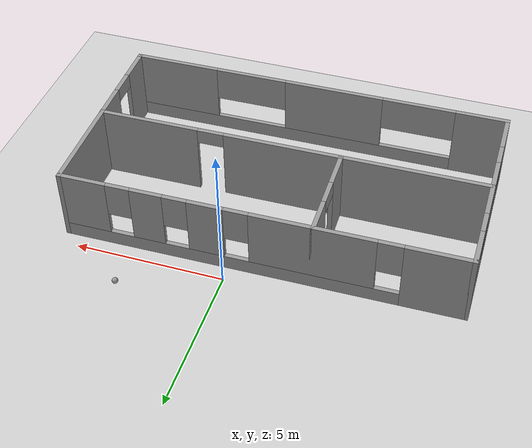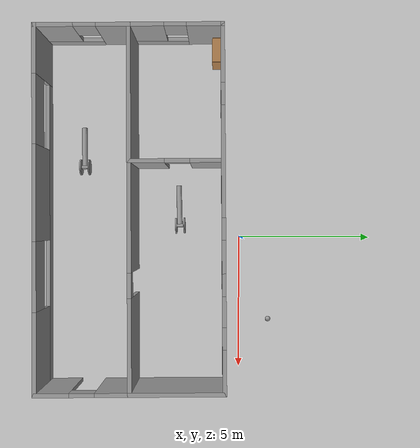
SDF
<sdf version="1.6">
 <world name="default">
  <plugin name="welcome_message" filename="libwelcome_message.so"/>
  <light name="sun" type="directional">
   <pose>0 0 10 0 -0 0</pose>
   <diffuse>0.8 0.8 0.8 1</diffuse>
   <specular>0.2 0.2 0.2 1</specular>
   <attenuation>
    <range>1000</range>
    <constant>0.9</constant>
    <linear>0.01</linear>
    <quadratic>0.001</quadratic>
   </attenuation>
   <direction>-0.5 0.1 -0.9</direction>
  </light>
  <model name="ground_plane">
   <static>1</static>
   <link name="link">
    <collision name="collision">
     <geometry><plane><normal>0 0 1</normal><size>100 100</size></plane></geometry>
     <surface>
      <contact><collide_bitmask>65535</collide_bitmask></contact>
      <friction><ode><mu>100</mu><mu2>50</mu2></ode></friction>
     </surface>
    </collision>
    <visual name="visual">
     <cast_shadows>0</cast_shadows>
     <geometry><plane><normal>0 0 1</normal><size>100 100</size></plane></geometry>
     <material>
      <script><uri>file://media/materials/scripts/gazebo.material</uri><name>Gazebo/Grey</name></script>
     </material>
    </visual>
   </link>
  </model>
  <gravity>0 0 -9.8</gravity>
  <magnetic_field>6e-06 2.3e-05 -4.2e-05</magnetic_field>
  <atmosphere type="adiabatic"/>
  <physics name="default_physics" default="0" type="ode">
   <max_step_size>0.001</max_step_size>
   <real_time_factor>1</real_time_factor>
   <real_time_update_rate>1000</real_time_update_rate>
  </physics>
  <scene><ambient>0.4 0.4 0.4 1</ambient><background>0.7 0.7 0.7 1</background><shadows>1</shadows></scene>
  <spherical_coordinates>
   <surface_model>EARTH_WGS84</surface_model>
   <latitude_deg>0</latitude_deg>
   <longitude_deg>0</longitude_deg>
   <elevation>0</elevation>
   <heading_deg>0</heading_deg>
  </spherical_coordinates>
  <model name="Robo-Space.sdf">
   <link name="Wall_1">
    <pose>-6.55 1.675 0 0 0 -1.5708</pose>
    <visual name="Wall_1_Visual_0">
     <pose>-1.0675 0 1.25 0 -0 0</pose>
     <geometry><box><size>1.365 0.15 2.5</size></box></geometry>
     <material>
      <script><uri>file://media/materials/scripts/gazebo.material</uri><name>Gazebo/Grey</name></script>
      <ambient>1 1 1 1</ambient>
      <shader type="pixel"/>
      <diffuse>0.7 0.7 0.7 1</diffuse>
      <specular>0.01 0.01 0.01 1</specular>
      <emissive>0 0 0 1</emissive>
     </material>
     <meta><layer>0</layer></meta>
    </visual>
    <visual name="Wall_1_Visual_1">
     <pose>0.6825 0 0.25 0 -0 0</pose>
     <geometry><box><size>2.135 0.15 0.5</size></box></geometry>
     <material>
      <script><uri>file://media/materials/scripts/gazebo.material</uri><name>Gazebo/Grey</name></script>
      <ambient>1 1 1 1</ambient>
      <shader type="pixel"/>
      <diffuse>0.7 0.7 0.7 1</diffuse>
      <specular>0.01 0.01 0.01 1</specular>
      <emissive>0 0 0 1</emissive>
     </material>
     <meta><layer>0</layer></meta>
    </visual>
    <visual name="Wall_1_Visual_2">
     <pose>1.0825 0 1.5 0 -0 0</pose>
     <geometry><box><size>1.335 0.15 2</size></box></geometry>
     <material>
      <script><uri>file://media/materials/scripts/gazebo.material</uri><name>Gazebo/Grey</name></script>
      <ambient>1 1 1 1</ambient>
      <shader type="pixel"/>
      <diffuse>0.7 0.7 0.7 1</diffuse>
      <specular>0.01 0.01 0.01 1</specular>
      <emissive>0 0 0 1</emissive>
     </material>
     <meta><layer>0</layer></meta>
    </visual>
    <visual name="Wall_1_Visual_3">
     <pose>0.015 0 1.9 0 -0 0</pose>
     <geometry><box><size>0.8 0.15 1.2</size></box></geometry>
     <material>
      <script><uri>file://media/materials/scripts/gazebo.material</uri><name>Gazebo/Grey</name></script>
      <ambient>1 1 1 1</ambient>
      <shader type="pixel"/>
      <diffuse>0.7 0.7 0.7 1</diffuse>
      <specular>0.01 0.01 0.01 1</specular>
      <emissive>0 0 0 1</emissive>
     </material>
     <meta><layer>0</layer></meta>
    </visual>
    <collision name="Wall_1_Collision_0">
     <pose>-1.0675 0 1.25 0 -0 0</pose>
     <geometry><box><size>1.365 0.15 2.5</size></box></geometry>
     <surface>
      <friction>
       <ode><mu>1</mu><mu2>1</mu2><fdir1>0 0 0</fdir1><slip1>0</slip1><slip2>0</slip2></ode>
       <torsional>
        <coefficient>1</coefficient>
        <patch_radius>0</patch_radius>
        <surface_radius>0</surface_radius>
        <use_patch_radius>1</use_patch_radius>
        <ode><slip>0</slip></ode>
       </torsional>
      </friction>
      <bounce><restitution_coefficient>0</restitution_coefficient><threshold>1e+06</threshold></bounce>
      <contact>
       <collide_without_contact>0</collide_without_contact>
       <collide_without_contact_bitmask>1</collide_without_contact_bitmask>
       <collide_bitmask>1</collide_bitmask>
       <ode>
        <soft_cfm>0</soft_cfm>
        <soft_erp>0.2</soft_erp>
        <kp>1e+13</kp>
        <kd>1</kd>
        <max_vel>0.01</max_vel>
        <min_depth>0</min_depth>
       </ode>
       <bullet>
        <split_impulse>1</split_impulse>
        <split_impulse_penetration_threshold>-0.01</split_impulse_penetration_threshold>
        <soft_cfm>0</soft_cfm>
        <soft_erp>0.2</soft_erp>
        <kp>1e+13</kp>
        <kd>1</kd>
       </bullet>
      </contact>
     </surface>
    </collision>
    <collision name="Wall_1_Collision_1">
     <pose>0.6825 0 0.25 0 -0 0</pose>
     <geometry><box><size>2.135 0.15 0.5</size></box></geometry>
     <surface>
      <friction>
       <ode><mu>1</mu><mu2>1</mu2><fdir1>0 0 0</fdir1><slip1>0</slip1><slip2>0</slip2></ode>
       <torsional>
        <coefficient>1</coefficient>
        <patch_radius>0</patch_radius>
        <surface_radius>0</surface_radius>
        <use_patch_radius>1</use_patch_radius>
        <ode><slip>0</slip></ode>
       </torsional>
      </friction>
      <bounce><restitution_coefficient>0</restitution_coefficient><threshold>1e+06</threshold></bounce>
      <contact>
       <collide_without_contact>0</collide_without_contact>
       <collide_without_contact_bitmask>1</collide_without_contact_bitmask>
       <collide_bitmask>1</collide_bitmask>
       <ode>
        <soft_cfm>0</soft_cfm>
        <soft_erp>0.2</soft_erp>
        <kp>1e+13</kp>
        <kd>1</kd>
        <max_vel>0.01</max_vel>
        <min_depth>0</min_depth>
       </ode>
       <bullet>
        <split_impulse>1</split_impulse>
        <split_impulse_penetration_threshold>-0.01</split_impulse_penetration_threshold>
        <soft_cfm>0</soft_cfm>
        <soft_erp>0.2</soft_erp>
        <kp>1e+13</kp>
        <kd>1</kd>
       </bullet>
      </contact>
     </surface>
    </collision>
    <collision name="Wall_1_Collision_2">
     <pose>1.0825 0 1.5 0 -0 0</pose>
     <geometry><box><size>1.335 0.15 2</size></box></geometry>
     <surface>
      <friction>
       <ode><mu>1</mu><mu2>1</mu2><fdir1>0 0 0</fdir1><slip1>0</slip1><slip2>0</slip2></ode>
       <torsional>
        <coefficient>1</coefficient>
        <patch_radius>0</patch_radius>
        <surface_radius>0</surface_radius>
        <use_patch_radius>1</use_patch_radius>
        <ode><slip>0</slip></ode>
       </torsional>
      </friction>
      <bounce><restitution_coefficient>0</restitution_coefficient><threshold>1e+06</threshold></bounce>
      <contact>
       <collide_without_contact>0</collide_without_contact>
       <collide_without_contact_bitmask>1</collide_without_contact_bitmask>
       <collide_bitmask>1</collide_bitmask>
       <ode>
        <soft_cfm>0</soft_cfm>
        <soft_erp>0.2</soft_erp>
        <kp>1e+13</kp>
        <kd>1</kd>
        <max_vel>0.01</max_vel>
        <min_depth>0</min_depth>
       </ode>
       <bullet>
        <split_impulse>1</split_impulse>
        <split_impulse_penetration_threshold>-0.01</split_impulse_penetration_threshold>
        <soft_cfm>0</soft_cfm>
        <soft_erp>0.2</soft_erp>
        <kp>1e+13</kp>
        <kd>1</kd>
       </bullet>
      </contact>
     </surface>
    </collision>
    <collision name="Wall_1_Collision_3">
     <pose>0.015 0 1.9 0 -0 0</pose>
     <geometry><box><size>0.8 0.15 1.2</size></box></geometry>
     <surface>
      <friction>
       <ode><mu>1</mu><mu2>1</mu2><fdir1>0 0 0</fdir1><slip1>0</slip1><slip2>0</slip2></ode>
       <torsional>
        <coefficient>1</coefficient>
        <patch_radius>0</patch_radius>
        <surface_radius>0</surface_radius>
        <use_patch_radius>1</use_patch_radius>
        <ode><slip>0</slip></ode>
       </torsional>
      </friction>
      <bounce><restitution_coefficient>0</restitution_coefficient><threshold>1e+06</threshold></bounce>
      <contact>
       <collide_without_contact>0</collide_without_contact>
       <collide_without_contact_bitmask>1</collide_without_contact_bitmask>
       <collide_bitmask>1</collide_bitmask>
       <ode>
        <soft_cfm>0</soft_cfm>
        <soft_erp>0.2</soft_erp>
        <kp>1e+13</kp>
        <kd>1</kd>
        <max_vel>0.01</max_vel>
        <min_depth>0</min_depth>
       </ode>
       <bullet>
        <split_impulse>1</split_impulse>
        <split_impulse_penetration_threshold>-0.01</split_impulse_penetration_threshold>
        <soft_cfm>0</soft_cfm>
        <soft_erp>0.2</soft_erp>
        <kp>1e+13</kp>
        <kd>1</kd>
       </bullet>
      </contact>
     </surface>
    </collision>
   </link>
   <link name="Wall_10">
    <pose>0 -3.35 0 0 -0 0</pose>
    <visual name="Wall_10_Visual_0">
     <pose>-5.72 0 1.25 0 -0 0</pose>
     <geometry><box><size>1.81 0.15 2.5</size></box></geometry>
     <material>
      <script><uri>file://media/materials/scripts/gazebo.material</uri><name>Gazebo/Grey</name></script>
      <ambient>1 1 1 1</ambient>
      <shader type="pixel"/>
      <diffuse>0.7 0.7 0.7 1</diffuse>
      <specular>0.01 0.01 0.01 1</specular>
      <emissive>0 0 0 1</emissive>
     </material>
     <meta><layer>0</layer></meta>
    </visual>
    <visual name="Wall_10_Visual_1">
     <pose>0.905 0 0.25 0 -0 0</pose>
     <geometry><box><size>11.44 0.15 0.5</size></box></geometry>
     <material>
      <script><uri>file://media/materials/scripts/gazebo.material</uri><name>Gazebo/Grey</name></script>
      <ambient>1 1 1 1</ambient>
      <shader type="pixel"/>
      <diffuse>0.7 0.7 0.7 1</diffuse>
      <specular>0.01 0.01 0.01 1</specular>
      <emissive>0 0 0 1</emissive>
     </material>
     <meta><layer>0</layer></meta>
    </visual>
    <visual name="Wall_10_Visual_2">
     <pose>-0.5925 0 1.5 0 -0 0</pose>
     <geometry><box><size>3.445 0.15 2</size></box></geometry>
     <material>
      <script><uri>file://media/materials/scripts/gazebo.material</uri><name>Gazebo/Grey</name></script>
      <ambient>1 1 1 1</ambient>
      <shader type="pixel"/>
      <diffuse>0.7 0.7 0.7 1</diffuse>
      <specular>0.01 0.01 0.01 1</specular>
      <emissive>0 0 0 1</emissive>
     </material>
     <meta><layer>0</layer></meta>
    </visual>
    <visual name="Wall_10_Visual_3">
     <pose>5.1275 0 1.5 0 -0 0</pose>
     <geometry><box><size>2.995 0.15 2</size></box></geometry>
     <material>
      <script><uri>file://media/materials/scripts/gazebo.material</uri><name>Gazebo/Grey</name></script>
      <ambient>1 1 1 1</ambient>
      <shader type="pixel"/>
      <diffuse>0.7 0.7 0.7 1</diffuse>
      <specular>0.01 0.01 0.01 1</specular>
      <emissive>0 0 0 1</emissive>
     </material>
     <meta><layer>0</layer></meta>
    </visual>
    <visual name="Wall_10_Visual_4">
     <pose>-3.565 0 1.9 0 -0 0</pose>
     <geometry><box><size>2.5 0.15 1.2</size></box></geometry>
     <material>
      <script><uri>file://media/materials/scripts/gazebo.material</uri><name>Gazebo/Grey</name></script>
      <ambient>1 1 1 1</ambient>
      <shader type="pixel"/>
      <diffuse>0.7 0.7 0.7 1</diffuse>
      <specular>0.01 0.01 0.01 1</specular>
      <emissive>0 0 0 1</emissive>
     </material>
     <meta><layer>0</layer></meta>
    </visual>
    <visual name="Wall_10_Visual_5">
     <pose>2.38 0 1.9 0 -0 0</pose>
     <geometry><box><size>2.5 0.15 1.2</size></box></geometry>
     <material>
      <script><uri>file://media/materials/scripts/gazebo.material</uri><name>Gazebo/Grey</name></script>
      <ambient>1 1 1 1</ambient>
      <shader type="pixel"/>
      <diffuse>0.7 0.7 0.7 1</diffuse>
      <specular>0.01 0.01 0.01 1</specular>
      <emissive>0 0 0 1</emissive>
     </material>
     <meta><layer>0</layer></meta>
    </visual>
    <collision name="Wall_10_Collision_0">
     <pose>-5.72 0 1.25 0 -0 0</pose>
     <geometry><box><size>1.81 0.15 2.5</size></box></geometry>
     <surface>
      <friction>
       <ode><mu>1</mu><mu2>1</mu2><fdir1>0 0 0</fdir1><slip1>0</slip1><slip2>0</slip2></ode>
       <torsional>
        <coefficient>1</coefficient>
        <patch_radius>0</patch_radius>
        <surface_radius>0</surface_radius>
        <use_patch_radius>1</use_patch_radius>
        <ode><slip>0</slip></ode>
       </torsional>
      </friction>
      <bounce><restitution_coefficient>0</restitution_coefficient><threshold>1e+06</threshold></bounce>
      <contact>
       <collide_without_contact>0</collide_without_contact>
       <collide_without_contact_bitmask>1</collide_without_contact_bitmask>
       <collide_bitmask>1</collide_bitmask>
       <ode>
        <soft_cfm>0</soft_cfm>
        <soft_erp>0.2</soft_erp>
        <kp>1e+13</kp>
        <kd>1</kd>
        <max_vel>0.01</max_vel>
        <min_depth>0</min_depth>
       </ode>
       <bullet>
        <split_impulse>1</split_impulse>
        <split_impulse_penetration_threshold>-0.01</split_impulse_penetration_threshold>
        <soft_cfm>0</soft_cfm>
        <soft_erp>0.2</soft_erp>
        <kp>1e+13</kp>
        <kd>1</kd>
       </bullet>
      </contact>
     </surface>
    </collision>
    <collision name="Wall_10_Collision_1">
     <pose>0.905 0 0.25 0 -0 0</pose>
     <geometry><box><size>11.44 0.15 0.5</size></box></geometry>
     <surface>
      <friction>
       <ode><mu>1</mu><mu2>1</mu2><fdir1>0 0 0</fdir1><slip1>0</slip1><slip2>0</slip2></ode>
       <torsional>
        <coefficient>1</coefficient>
        <patch_radius>0</patch_radius>
        <surface_radius>0</surface_radius>
        <use_patch_radius>1</use_patch_radius>
        <ode><slip>0</slip></ode>
       </torsional>
      </friction>
      <bounce><restitution_coefficient>0</restitution_coefficient><threshold>1e+06</threshold></bounce>
      <contact>
       <collide_without_contact>0</collide_without_contact>
       <collide_without_contact_bitmask>1</collide_without_contact_bitmask>
       <collide_bitmask>1</collide_bitmask>
       <ode>
        <soft_cfm>0</soft_cfm>
        <soft_erp>0.2</soft_erp>
        <kp>1e+13</kp>
        <kd>1</kd>
        <max_vel>0.01</max_vel>
        <min_depth>0</min_depth>
       </ode>
       <bullet>
        <split_impulse>1</split_impulse>
        <split_impulse_penetration_threshold>-0.01</split_impulse_penetration_threshold>
        <soft_cfm>0</soft_cfm>
        <soft_erp>0.2</soft_erp>
        <kp>1e+13</kp>
        <kd>1</kd>
       </bullet>
      </contact>
     </surface>
    </collision>
    <collision name="Wall_10_Collision_2">
     <pose>-0.5925 0 1.5 0 -0 0</pose>
     <geometry><box><size>3.445 0.15 2</size></box></geometry>
     <surface>
      <friction>
       <ode><mu>1</mu><mu2>1</mu2><fdir1>0 0 0</fdir1><slip1>0</slip1><slip2>0</slip2></ode>
       <torsional>
        <coefficient>1</coefficient>
        <patch_radius>0</patch_radius>
        <surface_radius>0</surface_radius>
        <use_patch_radius>1</use_patch_radius>
        <ode><slip>0</slip></ode>
       </torsional>
      </friction>
      <bounce><restitution_coefficient>0</restitution_coefficient><threshold>1e+06</threshold></bounce>
      <contact>
       <collide_without_contact>0</collide_without_contact>
       <collide_without_contact_bitmask>1</collide_without_contact_bitmask>
       <collide_bitmask>1</collide_bitmask>
       <ode>
        <soft_cfm>0</soft_cfm>
        <soft_erp>0.2</soft_erp>
        <kp>1e+13</kp>
        <kd>1</kd>
        <max_vel>0.01</max_vel>
        <min_depth>0</min_depth>
       </ode>
       <bullet>
        <split_impulse>1</split_impulse>
        <split_impulse_penetration_threshold>-0.01</split_impulse_penetration_threshold>
        <soft_cfm>0</soft_cfm>
        <soft_erp>0.2</soft_erp>
        <kp>1e+13</kp>
        <kd>1</kd>
       </bullet>
      </contact>
     </surface>
    </collision>
    <collision name="Wall_10_Collision_3">
     <pose>5.1275 0 1.5 0 -0 0</pose>
     <geometry><box><size>2.995 0.15 2</size></box></geometry>
     <surface>
      <friction>
       <ode><mu>1</mu><mu2>1</mu2><fdir1>0 0 0</fdir1><slip1>0</slip1><slip2>0</slip2></ode>
       <torsional>
        <coefficient>1</coefficient>
        <patch_radius>0</patch_radius>
        <surface_radius>0</surface_radius>
        <use_patch_radius>1</use_patch_radius>
        <ode><slip>0</slip></ode>
       </torsional>
      </friction>
      <bounce><restitution_coefficient>0</restitution_coefficient><threshold>1e+06</threshold></bounce>
      <contact>
       <collide_without_contact>0</collide_without_contact>
       <collide_without_contact_bitmask>1</collide_without_contact_bitmask>
       <collide_bitmask>1</collide_bitmask>
       <ode>
        <soft_cfm>0</soft_cfm>
        <soft_erp>0.2</soft_erp>
        <kp>1e+13</kp>
        <kd>1</kd>
        <max_vel>0.01</max_vel>
        <min_depth>0</min_depth>
       </ode>
       <bullet>
        <split_impulse>1</split_impulse>
        <split_impulse_penetration_threshold>-0.01</split_impulse_penetration_threshold>
        <soft_cfm>0</soft_cfm>
        <soft_erp>0.2</soft_erp>
        <kp>1e+13</kp>
        <kd>1</kd>
       </bullet>
      </contact>
     </surface>
    </collision>
    <collision name="Wall_10_Collision_4">
     <pose>-3.565 0 1.9 0 -0 0</pose>
     <geometry><box><size>2.5 0.15 1.2</size></box></geometry>
     <surface>
      <friction>
       <ode><mu>1</mu><mu2>1</mu2><fdir1>0 0 0</fdir1><slip1>0</slip1><slip2>0</slip2></ode>
       <torsional>
        <coefficient>1</coefficient>
        <patch_radius>0</patch_radius>
        <surface_radius>0</surface_radius>
        <use_patch_radius>1</use_patch_radius>
        <ode><slip>0</slip></ode>
       </torsional>
      </friction>
      <bounce><restitution_coefficient>0</restitution_coefficient><threshold>1e+06</threshold></bounce>
      <contact>
       <collide_without_contact>0</collide_without_contact>
       <collide_without_contact_bitmask>1</collide_without_contact_bitmask>
       <collide_bitmask>1</collide_bitmask>
       <ode>
        <soft_cfm>0</soft_cfm>
        <soft_erp>0.2</soft_erp>
        <kp>1e+13</kp>
        <kd>1</kd>
        <max_vel>0.01</max_vel>
        <min_depth>0</min_depth>
       </ode>
       <bullet>
        <split_impulse>1</split_impulse>
        <split_impulse_penetration_threshold>-0.01</split_impulse_penetration_threshold>
        <soft_cfm>0</soft_cfm>
        <soft_erp>0.2</soft_erp>
        <kp>1e+13</kp>
        <kd>1</kd>
       </bullet>
      </contact>
     </surface>
    </collision>
    <collision name="Wall_10_Collision_5">
     <pose>2.38 0 1.9 0 -0 0</pose>
     <geometry><box><size>2.5 0.15 1.2</size></box></geometry>
     <surface>
      <friction>
       <ode><mu>1</mu><mu2>1</mu2><fdir1>0 0 0</fdir1><slip1>0</slip1><slip2>0</slip2></ode>
       <torsional>
        <coefficient>1</coefficient>
        <patch_radius>0</patch_radius>
        <surface_radius>0</surface_radius>
        <use_patch_radius>1</use_patch_radius>
        <ode><slip>0</slip></ode>
       </torsional>
      </friction>
      <bounce><restitution_coefficient>0</restitution_coefficient><threshold>1e+06</threshold></bounce>
      <contact>
       <collide_without_contact>0</collide_without_contact>
       <collide_without_contact_bitmask>1</collide_without_contact_bitmask>
       <collide_bitmask>1</collide_bitmask>
       <ode>
        <soft_cfm>0</soft_cfm>
        <soft_erp>0.2</soft_erp>
        <kp>1e+13</kp>
        <kd>1</kd>
        <max_vel>0.01</max_vel>
        <min_depth>0</min_depth>
       </ode>
       <bullet>
        <split_impulse>1</split_impulse>
        <split_impulse_penetration_threshold>-0.01</split_impulse_penetration_threshold>
        <soft_cfm>0</soft_cfm>
        <soft_erp>0.2</soft_erp>
        <kp>1e+13</kp>
        <kd>1</kd>
       </bullet>
      </contact>
     </surface>
    </collision>
   </link>
   <link name="Wall_12">
    <pose>6.55 -1.675 0 0 0 -1.5708</pose>
    <visual name="Wall_12_Visual_0">
     <pose>-1.0975 0 1.25 0 -0 0</pose>
     <geometry><box><size>1.305 0.15 2.5</size></box></geometry>
     <material>
      <script><uri>file://media/materials/scripts/gazebo.material</uri><name>Gazebo/Grey</name></script>
      <ambient>1 1 1 1</ambient>
      <shader type="pixel"/>
      <diffuse>0.7 0.7 0.7 1</diffuse>
      <specular>0.01 0.01 0.01 1</specular>
      <emissive>0 0 0 1</emissive>
     </material>
     <meta><layer>0</layer></meta>
    </visual>
    <visual name="Wall_12_Visual_1">
     <pose>1.1025 0 1.25 0 -0 0</pose>
     <geometry><box><size>1.295 0.15 2.5</size></box></geometry>
     <material>
      <script><uri>file://media/materials/scripts/gazebo.material</uri><name>Gazebo/Grey</name></script>
      <ambient>1 1 1 1</ambient>
      <shader type="pixel"/>
      <diffuse>0.7 0.7 0.7 1</diffuse>
      <specular>0.01 0.01 0.01 1</specular>
      <emissive>0 0 0 1</emissive>
     </material>
     <meta><layer>0</layer></meta>
    </visual>
    <visual name="Wall_12_Visual_2">
     <pose>0.005 0 2.25 0 -0 0</pose>
     <geometry><box><size>0.9 0.15 0.5</size></box></geometry>
     <material>
      <script><uri>file://media/materials/scripts/gazebo.material</uri><name>Gazebo/Grey</name></script>
      <ambient>1 1 1 1</ambient>
      <shader type="pixel"/>
      <diffuse>0.7 0.7 0.7 1</diffuse>
      <specular>0.01 0.01 0.01 1</specular>
      <emissive>0 0 0 1</emissive>
     </material>
     <meta><layer>0</layer></meta>
    </visual>
    <collision name="Wall_12_Collision_0">
     <pose>-1.0975 0 1.25 0 -0 0</pose>
     <geometry><box><size>1.305 0.15 2.5</size></box></geometry>
     <surface>
      <friction>
       <ode><mu>1</mu><mu2>1</mu2><fdir1>0 0 0</fdir1><slip1>0</slip1><slip2>0</slip2></ode>
       <torsional>
        <coefficient>1</coefficient>
        <patch_radius>0</patch_radius>
        <surface_radius>0</surface_radius>
        <use_patch_radius>1</use_patch_radius>
        <ode><slip>0</slip></ode>
       </torsional>
      </friction>
      <bounce><restitution_coefficient>0</restitution_coefficient><threshold>1e+06</threshold></bounce>
      <contact>
       <collide_without_contact>0</collide_without_contact>
       <collide_without_contact_bitmask>1</collide_without_contact_bitmask>
       <collide_bitmask>1</collide_bitmask>
       <ode>
        <soft_cfm>0</soft_cfm>
        <soft_erp>0.2</soft_erp>
        <kp>1e+13</kp>
        <kd>1</kd>
        <max_vel>0.01</max_vel>
        <min_depth>0</min_depth>
       </ode>
       <bullet>
        <split_impulse>1</split_impulse>
        <split_impulse_penetration_threshold>-0.01</split_impulse_penetration_threshold>
        <soft_cfm>0</soft_cfm>
        <soft_erp>0.2</soft_erp>
        <kp>1e+13</kp>
        <kd>1</kd>
       </bullet>
      </contact>
     </surface>
    </collision>
    <collision name="Wall_12_Collision_2">
     <pose>0.005 0 2.25 0 -0 0</pose>
     <geometry><box><size>0.9 0.15 0.5</size></box></geometry>
     <surface>
      <friction>
       <ode><mu>1</mu><mu2>1</mu2><fdir1>0 0 0</fdir1><slip1>0</slip1><slip2>0</slip2></ode>
       <torsional>
        <coefficient>1</coefficient>
        <patch_radius>0</patch_radius>
        <surface_radius>0</surface_radius>
        <use_patch_radius>1</use_patch_radius>
        <ode><slip>0</slip></ode>
       </torsional>
      </friction>
      <bounce><restitution_coefficient>0</restitution_coefficient><threshold>1e+06</threshold></bounce>
      <contact>
       <collide_without_contact>0</collide_without_contact>
       <collide_without_contact_bitmask>1</collide_without_contact_bitmask>
       <collide_bitmask>1</collide_bitmask>
       <ode>
        <soft_cfm>0</soft_cfm>
        <soft_erp>0.2</soft_erp>
        <kp>1e+13</kp>
        <kd>1</kd>
        <max_vel>0.01</max_vel>
        <min_depth>0</min_depth>
       </ode>
       <bullet>
        <split_impulse>1</split_impulse>
        <split_impulse_penetration_threshold>-0.01</split_impulse_penetration_threshold>
        <soft_cfm>0</soft_cfm>
        <soft_erp>0.2</soft_erp>
        <kp>1e+13</kp>
        <kd>1</kd>
       </bullet>
      </contact>
     </surface>
    </collision>
    <collision name="Wall_12_Collision_1">
     <pose>1.1025 0 1.25 0 -0 0</pose>
     <geometry><box><size>1.295 0.15 2.5</size></box></geometry>
     <surface>
      <friction>
       <ode><mu>1</mu><mu2>1</mu2><fdir1>0 0 0</fdir1><slip1>0</slip1><slip2>0</slip2></ode>
       <torsional>
        <coefficient>1</coefficient>
        <patch_radius>0</patch_radius>
        <surface_radius>0</surface_radius>
        <use_patch_radius>1</use_patch_radius>
        <ode><slip>0</slip></ode>
       </torsional>
      </friction>
      <bounce><restitution_coefficient>0</restitution_coefficient><threshold>1e+06</threshold></bounce>
      <contact>
       <collide_without_contact>0</collide_without_contact>
       <collide_without_contact_bitmask>1</collide_without_contact_bitmask>
       <collide_bitmask>1</collide_bitmask>
       <ode>
        <soft_cfm>0</soft_cfm>
        <soft_erp>0.2</soft_erp>
        <kp>1e+13</kp>
        <kd>1</kd>
        <max_vel>0.01</max_vel>
        <min_depth>0</min_depth>
       </ode>
       <bullet>
        <split_impulse>1</split_impulse>
        <split_impulse_penetration_threshold>-0.01</split_impulse_penetration_threshold>
        <soft_cfm>0</soft_cfm>
        <soft_erp>0.2</soft_erp>
        <kp>1e+13</kp>
        <kd>1</kd>
       </bullet>
      </contact>
     </surface>
    </collision>
   </link>
   <link name="Wall_2">
    <pose>-4.125 0 0 0 -0 0</pose>
    <visual name="Wall_2_Visual">
     <pose>0 0 1.25 0 -0 0</pose>
     <geometry><box><size>5 0.15 2.5</size></box></geometry>
     <material>
      <script><uri>file://media/materials/scripts/gazebo.material</uri><name>Gazebo/Grey</name></script>
      <ambient>1 1 1 1</ambient>
      <shader type="pixel"/>
      <diffuse>0.7 0.7 0.7 1</diffuse>
      <specular>0.01 0.01 0.01 1</specular>
      <emissive>0 0 0 1</emissive>
     </material>
     <meta><layer>0</layer></meta>
    </visual>
    <collision name="Wall_2_Collision">
     <pose>0 0 1.25 0 -0 0</pose>
     <geometry><box><size>5 0.15 2.5</size></box></geometry>
     <surface>
      <friction>
       <ode><mu>1</mu><mu2>1</mu2><fdir1>0 0 0</fdir1><slip1>0</slip1><slip2>0</slip2></ode>
       <torsional>
        <coefficient>1</coefficient>
        <patch_radius>0</patch_radius>
        <surface_radius>0</surface_radius>
        <use_patch_radius>1</use_patch_radius>
        <ode><slip>0</slip></ode>
       </torsional>
      </friction>
      <bounce><restitution_coefficient>0</restitution_coefficient><threshold>1e+06</threshold></bounce>
      <contact>
       <collide_without_contact>0</collide_without_contact>
       <collide_without_contact_bitmask>1</collide_without_contact_bitmask>
       <collide_bitmask>1</collide_bitmask>
       <ode>
        <soft_cfm>0</soft_cfm>
        <soft_erp>0.2</soft_erp>
        <kp>1e+13</kp>
        <kd>1</kd>
        <max_vel>0.01</max_vel>
        <min_depth>0</min_depth>
       </ode>
       <bullet>
        <split_impulse>1</split_impulse>
        <split_impulse_penetration_threshold>-0.01</split_impulse_penetration_threshold>
        <soft_cfm>0</soft_cfm>
        <soft_erp>0.2</soft_erp>
        <kp>1e+13</kp>
        <kd>1</kd>
       </bullet>
      </contact>
     </surface>
    </collision>
   </link>
   <link name="Wall_3">
    <pose>-1.7 1.675 0 0 -0 1.5708</pose>
    <visual name="Wall_3_Visual_0">
     <pose>-1.0825 0 1.25 0 -0 0</pose>
     <geometry><box><size>1.335 0.15 2.5</size></box></geometry>
     <material>
      <script><uri>file://media/materials/scripts/gazebo.material</uri><name>Gazebo/Grey</name></script>
      <ambient>1 1 1 1</ambient>
      <shader type="pixel"/>
      <diffuse>0.7 0.7 0.7 1</diffuse>
      <specular>0.01 0.01 0.01 1</specular>
      <emissive>0 0 0 1</emissive>
     </material>
     <meta><layer>0</layer></meta>
    </visual>
    <visual name="Wall_3_Visual_1">
     <pose>1.1175 0 1.25 0 -0 0</pose>
     <geometry><box><size>1.265 0.15 2.5</size></box></geometry>
     <material>
      <script><uri>file://media/materials/scripts/gazebo.material</uri><name>Gazebo/Grey</name></script>
      <ambient>1 1 1 1</ambient>
      <shader type="pixel"/>
      <diffuse>0.7 0.7 0.7 1</diffuse>
      <specular>0.01 0.01 0.01 1</specular>
      <emissive>0 0 0 1</emissive>
     </material>
     <meta><layer>0</layer></meta>
    </visual>
    <visual name="Wall_3_Visual_2">
     <pose>0.035 0 2.25 0 -0 0</pose>
     <geometry><box><size>0.9 0.15 0.5</size></box></geometry>
     <material>
      <script><uri>file://media/materials/scripts/gazebo.material</uri><name>Gazebo/Grey</name></script>
      <ambient>1 1 1 1</ambient>
      <shader type="pixel"/>
      <diffuse>0.7 0.7 0.7 1</diffuse>
      <specular>0.01 0.01 0.01 1</specular>
      <emissive>0 0 0 1</emissive>
     </material>
     <meta><layer>0</layer></meta>
    </visual>
    <collision name="Wall_3_Collision_0">
     <pose>-1.0825 0 1.25 0 -0 0</pose>
     <geometry><box><size>1.335 0.15 2.5</size></box></geometry>
     <surface>
      <friction>
       <ode><mu>1</mu><mu2>1</mu2><fdir1>0 0 0</fdir1><slip1>0</slip1><slip2>0</slip2></ode>
       <torsional>
        <coefficient>1</coefficient>
        <patch_radius>0</patch_radius>
        <surface_radius>0</surface_radius>
        <use_patch_radius>1</use_patch_radius>
        <ode><slip>0</slip></ode>
       </torsional>
      </friction>
      <bounce><restitution_coefficient>0</restitution_coefficient><threshold>1e+06</threshold></bounce>
      <contact>
       <collide_without_contact>0</collide_without_contact>
       <collide_without_contact_bitmask>1</collide_without_contact_bitmask>
       <collide_bitmask>1</collide_bitmask>
       <ode>
        <soft_cfm>0</soft_cfm>
        <soft_erp>0.2</soft_erp>
        <kp>1e+13</kp>
        <kd>1</kd>
        <max_vel>0.01</max_vel>
        <min_depth>0</min_depth>
       </ode>
       <bullet>
        <split_impulse>1</split_impulse>
        <split_impulse_penetration_threshold>-0.01</split_impulse_penetration_threshold>
        <soft_cfm>0</soft_cfm>
        <soft_erp>0.2</soft_erp>
        <kp>1e+13</kp>
        <kd>1</kd>
       </bullet>
      </contact>
     </surface>
    </collision>
    <collision name="Wall_3_Collision_1">
     <pose>1.1175 0 1.25 0 -0 0</pose>
     <geometry><box><size>1.265 0.15 2.5</size></box></geometry>
     <surface>
      <friction>
       <ode><mu>1</mu><mu2>1</mu2><fdir1>0 0 0</fdir1><slip1>0</slip1><slip2>0</slip2></ode>
       <torsional>
        <coefficient>1</coefficient>
        <patch_radius>0</patch_radius>
        <surface_radius>0</surface_radius>
        <use_patch_radius>1</use_patch_radius>
        <ode><slip>0</slip></ode>
       </torsional>
      </friction>
      <bounce><restitution_coefficient>0</restitution_coefficient><threshold>1e+06</threshold></bounce>
      <contact>
       <collide_without_contact>0</collide_without_contact>
       <collide_without_contact_bitmask>1</collide_without_contact_bitmask>
       <collide_bitmask>1</collide_bitmask>
       <ode>
        <soft_cfm>0</soft_cfm>
        <soft_erp>0.2</soft_erp>
        <kp>1e+13</kp>
        <kd>1</kd>
        <max_vel>0.01</max_vel>
        <min_depth>0</min_depth>
       </ode>
       <bullet>
        <split_impulse>1</split_impulse>
        <split_impulse_penetration_threshold>-0.01</split_impulse_penetration_threshold>
        <soft_cfm>0</soft_cfm>
        <soft_erp>0.2</soft_erp>
        <kp>1e+13</kp>
        <kd>1</kd>
       </bullet>
      </contact>
     </surface>
    </collision>
    <collision name="Wall_3_Collision_2">
     <pose>0.035 0 2.25 0 -0 0</pose>
     <geometry><box><size>0.9 0.15 0.5</size></box></geometry>
     <surface>
      <friction>
       <ode><mu>1</mu><mu2>1</mu2><fdir1>0 0 0</fdir1><slip1>0</slip1><slip2>0</slip2></ode>
       <torsional>
        <coefficient>1</coefficient>
        <patch_radius>0</patch_radius>
        <surface_radius>0</surface_radius>
        <use_patch_radius>1</use_patch_radius>
        <ode><slip>0</slip></ode>
       </torsional>
      </friction>
      <bounce><restitution_coefficient>0</restitution_coefficient><threshold>1e+06</threshold></bounce>
      <contact>
       <collide_without_contact>0</collide_without_contact>
       <collide_without_contact_bitmask>1</collide_without_contact_bitmask>
       <collide_bitmask>1</collide_bitmask>
       <ode>
        <soft_cfm>0</soft_cfm>
        <soft_erp>0.2</soft_erp>
        <kp>1e+13</kp>
        <kd>1</kd>
        <max_vel>0.01</max_vel>
        <min_depth>0</min_depth>
       </ode>
       <bullet>
        <split_impulse>1</split_impulse>
        <split_impulse_penetration_threshold>-0.01</split_impulse_penetration_threshold>
        <soft_cfm>0</soft_cfm>
        <soft_erp>0.2</soft_erp>
        <kp>1e+13</kp>
        <kd>1</kd>
       </bullet>
      </contact>
     </surface>
    </collision>
   </link>
   <link name="Wall_5">
    <pose>0 3.35 0 0 -0 0</pose>
    <visual name="Wall_5_Visual_0">
     <pose>-5.5475 0 1.25 0 -0 0</pose>
     <geometry><box><size>2.155 0.15 2.5</size></box></geometry>
     <material>
      <script><uri>file://media/materials/scripts/gazebo.material</uri><name>Gazebo/Grey</name></script>
      <ambient>1 1 1 1</ambient>
      <shader type="pixel"/>
      <diffuse>0.7 0.7 0.7 1</diffuse>
      <specular>0.01 0.01 0.01 1</specular>
      <emissive>0 0 0 1</emissive>
     </material>
     <meta><layer>0</layer></meta>
    </visual>
    <visual name="Wall_5_Visual_1">
     <pose>1.0775 0 0.25 0 -0 0</pose>
     <geometry><box><size>11.095 0.15 0.5</size></box></geometry>
     <material>
      <script><uri>file://media/materials/scripts/gazebo.material</uri><name>Gazebo/Grey</name></script>
      <ambient>1 1 1 1</ambient>
      <shader type="pixel"/>
      <diffuse>0.7 0.7 0.7 1</diffuse>
      <specular>0.01 0.01 0.01 1</specular>
      <emissive>0 0 0 1</emissive>
     </material>
     <meta><layer>0</layer></meta>
    </visual>
    <visual name="Wall_5_Visual_2">
     <pose>-1.67 0 1.5 0 -0 0</pose>
     <geometry><box><size>4 0.15 2</size></box></geometry>
     <material>
      <script><uri>file://media/materials/scripts/gazebo.material</uri><name>Gazebo/Grey</name></script>
      <ambient>1 1 1 1</ambient>
      <shader type="pixel"/>
      <diffuse>0.7 0.7 0.7 1</diffuse>
      <specular>0.01 0.01 0.01 1</specular>
      <emissive>0 0 0 1</emissive>
     </material>
     <meta><layer>0</layer></meta>
    </visual>
    <visual name="Wall_5_Visual_3">
     <pose>1.72 0 1.5 0 -0 0</pose>
     <geometry><box><size>1.18 0.15 2</size></box></geometry>
     <material>
      <script><uri>file://media/materials/scripts/gazebo.material</uri><name>Gazebo/Grey</name></script>
      <ambient>1 1 1 1</ambient>
      <shader type="pixel"/>
      <diffuse>0.7 0.7 0.7 1</diffuse>
      <specular>0.01 0.01 0.01 1</specular>
      <emissive>0 0 0 1</emissive>
     </material>
     <meta><layer>0</layer></meta>
    </visual>
    <visual name="Wall_5_Visual_4">
     <pose>3.65 0 1.5 0 -0 0</pose>
     <geometry><box><size>1.08 0.15 2</size></box></geometry>
     <material>
      <script><uri>file://media/materials/scripts/gazebo.material</uri><name>Gazebo/Grey</name></script>
      <ambient>1 1 1 1</ambient>
      <shader type="pixel"/>
      <diffuse>0.7 0.7 0.7 1</diffuse>
      <specular>0.01 0.01 0.01 1</specular>
      <emissive>0 0 0 1</emissive>
     </material>
     <meta><layer>0</layer></meta>
    </visual>
    <visual name="Wall_5_Visual_5">
     <pose>5.8075 0 1.5 0 -0 0</pose>
     <geometry><box><size>1.635 0.15 2</size></box></geometry>
     <material>
      <script><uri>file://media/materials/scripts/gazebo.material</uri><name>Gazebo/Grey</name></script>
      <ambient>1 1 1 1</ambient>
      <shader type="pixel"/>
      <diffuse>0.7 0.7 0.7 1</diffuse>
      <specular>0.01 0.01 0.01 1</specular>
      <emissive>0 0 0 1</emissive>
     </material>
     <meta><layer>0</layer></meta>
    </visual>
    <visual name="Wall_5_Visual_6">
     <pose>-4.07 0 1.9 0 -0 0</pose>
     <geometry><box><size>0.8 0.15 1.2</size></box></geometry>
     <material>
      <script><uri>file://media/materials/scripts/gazebo.material</uri><name>Gazebo/Grey</name></script>
      <ambient>1 1 1 1</ambient>
      <shader type="pixel"/>
      <diffuse>0.7 0.7 0.7 1</diffuse>
      <specular>0.01 0.01 0.01 1</specular>
      <emissive>0 0 0 1</emissive>
     </material>
     <meta><layer>0</layer></meta>
    </visual>
    <visual name="Wall_5_Visual_7">
     <pose>0.73 0 1.9 0 -0 0</pose>
     <geometry><box><size>0.8 0.15 1.2</size></box></geometry>
     <material>
      <script><uri>file://media/materials/scripts/gazebo.material</uri><name>Gazebo/Grey</name></script>
      <ambient>1 1 1 1</ambient>
      <shader type="pixel"/>
      <diffuse>0.7 0.7 0.7 1</diffuse>
      <specular>0.01 0.01 0.01 1</specular>
      <emissive>0 0 0 1</emissive>
     </material>
     <meta><layer>0</layer></meta>
    </visual>
    <visual name="Wall_5_Visual_8">
     <pose>2.71 0 1.9 0 -0 0</pose>
     <geometry><box><size>0.8 0.15 1.2</size></box></geometry>
     <material>
      <script><uri>file://media/materials/scripts/gazebo.material</uri><name>Gazebo/Grey</name></script>
      <ambient>1 1 1 1</ambient>
      <shader type="pixel"/>
      <diffuse>0.7 0.7 0.7 1</diffuse>
      <specular>0.01 0.01 0.01 1</specular>
      <emissive>0 0 0 1</emissive>
     </material>
     <meta><layer>0</layer></meta>
    </visual>
    <visual name="Wall_5_Visual_9">
     <pose>4.59 0 1.9 0 -0 0</pose>
     <geometry><box><size>0.8 0.15 1.2</size></box></geometry>
     <material>
      <script><uri>file://media/materials/scripts/gazebo.material</uri><name>Gazebo/Grey</name></script>
      <ambient>1 1 1 1</ambient>
      <shader type="pixel"/>
      <diffuse>0.7 0.7 0.7 1</diffuse>
      <specular>0.01 0.01 0.01 1</specular>
      <emissive>0 0 0 1</emissive>
     </material>
     <meta><layer>0</layer></meta>
    </visual>
    <collision name="Wall_5_Collision_0">
     <pose>-5.5475 0 1.25 0 -0 0</pose>
     <geometry><box><size>2.155 0.15 2.5</size></box></geometry>
     <surface>
      <friction>
       <ode><mu>1</mu><mu2>1</mu2><fdir1>0 0 0</fdir1><slip1>0</slip1><slip2>0</slip2></ode>
       <torsional>
        <coefficient>1</coefficient>
        <patch_radius>0</patch_radius>
        <surface_radius>0</surface_radius>
        <use_patch_radius>1</use_patch_radius>
        <ode><slip>0</slip></ode>
       </torsional>
      </friction>
      <bounce><restitution_coefficient>0</restitution_coefficient><threshold>1e+06</threshold></bounce>
      <contact>
       <collide_without_contact>0</collide_without_contact>
       <collide_without_contact_bitmask>1</collide_without_contact_bitmask>
       <collide_bitmask>1</collide_bitmask>
       <ode>
        <soft_cfm>0</soft_cfm>
        <soft_erp>0.2</soft_erp>
        <kp>1e+13</kp>
        <kd>1</kd>
        <max_vel>0.01</max_vel>
        <min_depth>0</min_depth>
       </ode>
       <bullet>
        <split_impulse>1</split_impulse>
        <split_impulse_penetration_threshold>-0.01</split_impulse_penetration_threshold>
        <soft_cfm>0</soft_cfm>
        <soft_erp>0.2</soft_erp>
        <kp>1e+13</kp>
        <kd>1</kd>
       </bullet>
      </contact>
     </surface>
    </collision>
    <collision name="Wall_5_Collision_1">
     <pose>1.0775 0 0.25 0 -0 0</pose>
     <geometry><box><size>11.095 0.15 0.5</size></box></geometry>
     <surface>
      <friction>
       <ode><mu>1</mu><mu2>1</mu2><fdir1>0 0 0</fdir1><slip1>0</slip1><slip2>0</slip2></ode>
       <torsional>
        <coefficient>1</coefficient>
        <patch_radius>0</patch_radius>
        <surface_radius>0</surface_radius>
        <use_patch_radius>1</use_patch_radius>
        <ode><slip>0</slip></ode>
       </torsional>
      </friction>
      <bounce><restitution_coefficient>0</restitution_coefficient><threshold>1e+06</threshold></bounce>
      <contact>
       <collide_without_contact>0</collide_without_contact>
       <collide_without_contact_bitmask>1</collide_without_contact_bitmask>
       <collide_bitmask>1</collide_bitmask>
       <ode>
        <soft_cfm>0</soft_cfm>
        <soft_erp>0.2</soft_erp>
        <kp>1e+13</kp>
        <kd>1</kd>
        <max_vel>0.01</max_vel>
        <min_depth>0</min_depth>
       </ode>
       <bullet>
        <split_impulse>1</split_impulse>
        <split_impulse_penetration_threshold>-0.01</split_impulse_penetration_threshold>
        <soft_cfm>0</soft_cfm>
        <soft_erp>0.2</soft_erp>
        <kp>1e+13</kp>
        <kd>1</kd>
       </bullet>
      </contact>
     </surface>
    </collision>
    <collision name="Wall_5_Collision_2">
     <pose>-1.67 0 1.5 0 -0 0</pose>
     <geometry><box><size>4 0.15 2</size></box></geometry>
     <surface>
      <friction>
       <ode><mu>1</mu><mu2>1</mu2><fdir1>0 0 0</fdir1><slip1>0</slip1><slip2>0</slip2></ode>
       <torsional>
        <coefficient>1</coefficient>
        <patch_radius>0</patch_radius>
        <surface_radius>0</surface_radius>
        <use_patch_radius>1</use_patch_radius>
        <ode><slip>0</slip></ode>
       </torsional>
      </friction>
      <bounce><restitution_coefficient>0</restitution_coefficient><threshold>1e+06</threshold></bounce>
      <contact>
       <collide_without_contact>0</collide_without_contact>
       <collide_without_contact_bitmask>1</collide_without_contact_bitmask>
       <collide_bitmask>1</collide_bitmask>
       <ode>
        <soft_cfm>0</soft_cfm>
        <soft_erp>0.2</soft_erp>
        <kp>1e+13</kp>
        <kd>1</kd>
        <max_vel>0.01</max_vel>
        <min_depth>0</min_depth>
       </ode>
       <bullet>
        <split_impulse>1</split_impulse>
        <split_impulse_penetration_threshold>-0.01</split_impulse_penetration_threshold>
        <soft_cfm>0</soft_cfm>
        <soft_erp>0.2</soft_erp>
        <kp>1e+13</kp>
        <kd>1</kd>
       </bullet>
      </contact>
     </surface>
    </collision>
    <collision name="Wall_5_Collision_3">
     <pose>1.72 0 1.5 0 -0 0</pose>
     <geometry><box><size>1.18 0.15 2</size></box></geometry>
     <surface>
      <friction>
       <ode><mu>1</mu><mu2>1</mu2><fdir1>0 0 0</fdir1><slip1>0</slip1><slip2>0</slip2></ode>
       <torsional>
        <coefficient>1</coefficient>
        <patch_radius>0</patch_radius>
        <surface_radius>0</surface_radius>
        <use_patch_radius>1</use_patch_radius>
        <ode><slip>0</slip></ode>
       </torsional>
      </friction>
      <bounce><restitution_coefficient>0</restitution_coefficient><threshold>1e+06</threshold></bounce>
      <contact>
       <collide_without_contact>0</collide_without_contact>
       <collide_without_contact_bitmask>1</collide_without_contact_bitmask>
       <collide_bitmask>1</collide_bitmask>
       <ode>
        <soft_cfm>0</soft_cfm>
        <soft_erp>0.2</soft_erp>
        <kp>1e+13</kp>
        <kd>1</kd>
        <max_vel>0.01</max_vel>
        <min_depth>0</min_depth>
       </ode>
       <bullet>
        <split_impulse>1</split_impulse>
        <split_impulse_penetration_threshold>-0.01</split_impulse_penetration_threshold>
        <soft_cfm>0</soft_cfm>
        <soft_erp>0.2</soft_erp>
        <kp>1e+13</kp>
        <kd>1</kd>
       </bullet>
      </contact>
     </surface>
    </collision>
    <collision name="Wall_5_Collision_4">
     <pose>3.65 0 1.5 0 -0 0</pose>
     <geometry><box><size>1.08 0.15 2</size></box></geometry>
     <surface>
      <friction>
       <ode><mu>1</mu><mu2>1</mu2><fdir1>0 0 0</fdir1><slip1>0</slip1><slip2>0</slip2></ode>
       <torsional>
        <coefficient>1</coefficient>
        <patch_radius>0</patch_radius>
        <surface_radius>0</surface_radius>
        <use_patch_radius>1</use_patch_radius>
        <ode><slip>0</slip></ode>
       </torsional>
      </friction>
      <bounce><restitution_coefficient>0</restitution_coefficient><threshold>1e+06</threshold></bounce>
      <contact>
       <collide_without_contact>0</collide_without_contact>
       <collide_without_contact_bitmask>1</collide_without_contact_bitmask>
       <collide_bitmask>1</collide_bitmask>
       <ode>
        <soft_cfm>0</soft_cfm>
        <soft_erp>0.2</soft_erp>
        <kp>1e+13</kp>
        <kd>1</kd>
        <max_vel>0.01</max_vel>
        <min_depth>0</min_depth>
       </ode>
       <bullet>
        <split_impulse>1</split_impulse>
        <split_impulse_penetration_threshold>-0.01</split_impulse_penetration_threshold>
        <soft_cfm>0</soft_cfm>
        <soft_erp>0.2</soft_erp>
        <kp>1e+13</kp>
        <kd>1</kd>
       </bullet>
      </contact>
     </surface>
    </collision>
    <collision name="Wall_5_Collision_5">
     <pose>5.8075 0 1.5 0 -0 0</pose>
     <geometry><box><size>1.635 0.15 2</size></box></geometry>
     <surface>
      <friction>
       <ode><mu>1</mu><mu2>1</mu2><fdir1>0 0 0</fdir1><slip1>0</slip1><slip2>0</slip2></ode>
       <torsional>
        <coefficient>1</coefficient>
        <patch_radius>0</patch_radius>
        <surface_radius>0</surface_radius>
        <use_patch_radius>1</use_patch_radius>
        <ode><slip>0</slip></ode>
       </torsional>
      </friction>
      <bounce><restitution_coefficient>0</restitution_coefficient><threshold>1e+06</threshold></bounce>
      <contact>
       <collide_without_contact>0</collide_without_contact>
       <collide_without_contact_bitmask>1</collide_without_contact_bitmask>
       <collide_bitmask>1</collide_bitmask>
       <ode>
        <soft_cfm>0</soft_cfm>
        <soft_erp>0.2</soft_erp>
        <kp>1e+13</kp>
        <kd>1</kd>
        <max_vel>0.01</max_vel>
        <min_depth>0</min_depth>
       </ode>
       <bullet>
        <split_impulse>1</split_impulse>
        <split_impulse_penetration_threshold>-0.01</split_impulse_penetration_threshold>
        <soft_cfm>0</soft_cfm>
        <soft_erp>0.2</soft_erp>
        <kp>1e+13</kp>
        <kd>1</kd>
       </bullet>
      </contact>
     </surface>
    </collision>
    <collision name="Wall_5_Collision_6">
     <pose>-4.07 0 1.9 0 -0 0</pose>
     <geometry><box><size>0.8 0.15 1.2</size></box></geometry>
     <surface>
      <friction>
       <ode><mu>1</mu><mu2>1</mu2><fdir1>0 0 0</fdir1><slip1>0</slip1><slip2>0</slip2></ode>
       <torsional>
        <coefficient>1</coefficient>
        <patch_radius>0</patch_radius>
        <surface_radius>0</surface_radius>
        <use_patch_radius>1</use_patch_radius>
        <ode><slip>0</slip></ode>
       </torsional>
      </friction>
      <bounce><restitution_coefficient>0</restitution_coefficient><threshold>1e+06</threshold></bounce>
      <contact>
       <collide_without_contact>0</collide_without_contact>
       <collide_without_contact_bitmask>1</collide_without_contact_bitmask>
       <collide_bitmask>1</collide_bitmask>
       <ode>
        <soft_cfm>0</soft_cfm>
        <soft_erp>0.2</soft_erp>
        <kp>1e+13</kp>
        <kd>1</kd>
        <max_vel>0.01</max_vel>
        <min_depth>0</min_depth>
       </ode>
       <bullet>
        <split_impulse>1</split_impulse>
        <split_impulse_penetration_threshold>-0.01</split_impulse_penetration_threshold>
        <soft_cfm>0</soft_cfm>
        <soft_erp>0.2</soft_erp>
        <kp>1e+13</kp>
        <kd>1</kd>
       </bullet>
      </contact>
     </surface>
    </collision>
    <collision name="Wall_5_Collision_7">
     <pose>0.73 0 1.9 0 -0 0</pose>
     <geometry><box><size>0.8 0.15 1.2</size></box></geometry>
     <surface>
      <friction>
       <ode><mu>1</mu><mu2>1</mu2><fdir1>0 0 0</fdir1><slip1>0</slip1><slip2>0</slip2></ode>
       <torsional>
        <coefficient>1</coefficient>
        <patch_radius>0</patch_radius>
        <surface_radius>0</surface_radius>
        <use_patch_radius>1</use_patch_radius>
        <ode><slip>0</slip></ode>
       </torsional>
      </friction>
      <bounce><restitution_coefficient>0</restitution_coefficient><threshold>1e+06</threshold></bounce>
      <contact>
       <collide_without_contact>0</collide_without_contact>
       <collide_without_contact_bitmask>1</collide_without_contact_bitmask>
       <collide_bitmask>1</collide_bitmask>
       <ode>
        <soft_cfm>0</soft_cfm>
        <soft_erp>0.2</soft_erp>
        <kp>1e+13</kp>
        <kd>1</kd>
        <max_vel>0.01</max_vel>
        <min_depth>0</min_depth>
       </ode>
       <bullet>
        <split_impulse>1</split_impulse>
        <split_impulse_penetration_threshold>-0.01</split_impulse_penetration_threshold>
        <soft_cfm>0</soft_cfm>
        <soft_erp>0.2</soft_erp>
        <kp>1e+13</kp>
        <kd>1</kd>
       </bullet>
      </contact>
     </surface>
    </collision>
    <collision name="Wall_5_Collision_8">
     <pose>2.71 0 1.9 0 -0 0</pose>
     <geometry><box><size>0.8 0.15 1.2</size></box></geometry>
     <surface>
      <friction>
       <ode><mu>1</mu><mu2>1</mu2><fdir1>0 0 0</fdir1><slip1>0</slip1><slip2>0</slip2></ode>
       <torsional>
        <coefficient>1</coefficient>
        <patch_radius>0</patch_radius>
        <surface_radius>0</surface_radius>
        <use_patch_radius>1</use_patch_radius>
        <ode><slip>0</slip></ode>
       </torsional>
      </friction>
      <bounce><restitution_coefficient>0</restitution_coefficient><threshold>1e+06</threshold></bounce>
      <contact>
       <collide_without_contact>0</collide_without_contact>
       <collide_without_contact_bitmask>1</collide_without_contact_bitmask>
       <collide_bitmask>1</collide_bitmask>
       <ode>
        <soft_cfm>0</soft_cfm>
        <soft_erp>0.2</soft_erp>
        <kp>1e+13</kp>
        <kd>1</kd>
        <max_vel>0.01</max_vel>
        <min_depth>0</min_depth>
       </ode>
       <bullet>
        <split_impulse>1</split_impulse>
        <split_impulse_penetration_threshold>-0.01</split_impulse_penetration_threshold>
        <soft_cfm>0</soft_cfm>
        <soft_erp>0.2</soft_erp>
        <kp>1e+13</kp>
        <kd>1</kd>
       </bullet>
      </contact>
     </surface>
    </collision>
    <collision name="Wall_5_Collision_9">
     <pose>4.59 0 1.9 0 -0 0</pose>
     <geometry><box><size>0.8 0.15 1.2</size></box></geometry>
     <surface>
      <friction>
       <ode><mu>1</mu><mu2>1</mu2><fdir1>0 0 0</fdir1><slip1>0</slip1><slip2>0</slip2></ode>
       <torsional>
        <coefficient>1</coefficient>
        <patch_radius>0</patch_radius>
        <surface_radius>0</surface_radius>
        <use_patch_radius>1</use_patch_radius>
        <ode><slip>0</slip></ode>
       </torsional>
      </friction>
      <bounce><restitution_coefficient>0</restitution_coefficient><threshold>1e+06</threshold></bounce>
      <contact>
       <collide_without_contact>0</collide_without_contact>
       <collide_without_contact_bitmask>1</collide_without_contact_bitmask>
       <collide_bitmask>1</collide_bitmask>
       <ode>
        <soft_cfm>0</soft_cfm>
        <soft_erp>0.2</soft_erp>
        <kp>1e+13</kp>
        <kd>1</kd>
        <max_vel>0.01</max_vel>
        <min_depth>0</min_depth>
       </ode>
       <bullet>
        <split_impulse>1</split_impulse>
        <split_impulse_penetration_threshold>-0.01</split_impulse_penetration_threshold>
        <soft_cfm>0</soft_cfm>
        <soft_erp>0.2</soft_erp>
        <kp>1e+13</kp>
        <kd>1</kd>
       </bullet>
      </contact>
     </surface>
    </collision>
   </link>
   <link name="Wall_6">
    <pose>6.55 1.675 0 0 0 -1.5708</pose>
    <visual name="Wall_6_Visual">
     <pose>0 0 1.25 0 -0 0</pose>
     <geometry><box><size>3.5 0.15 2.5</size></box></geometry>
     <material>
      <script><uri>file://media/materials/scripts/gazebo.material</uri><name>Gazebo/Grey</name></script>
      <ambient>1 1 1 1</ambient>
      <shader type="pixel"/>
      <diffuse>0.7 0.7 0.7 1</diffuse>
      <specular>0.01 0.01 0.01 1</specular>
      <emissive>0 0 0 1</emissive>
     </material>
     <meta><layer>0</layer></meta>
    </visual>
    <collision name="Wall_6_Collision">
     <pose>0 0 1.25 0 -0 0</pose>
     <geometry><box><size>3.5 0.15 2.5</size></box></geometry>
     <surface>
      <friction>
       <ode><mu>1</mu><mu2>1</mu2><fdir1>0 0 0</fdir1><slip1>0</slip1><slip2>0</slip2></ode>
       <torsional>
        <coefficient>1</coefficient>
        <patch_radius>0</patch_radius>
        <surface_radius>0</surface_radius>
        <use_patch_radius>1</use_patch_radius>
        <ode><slip>0</slip></ode>
       </torsional>
      </friction>
      <bounce><restitution_coefficient>0</restitution_coefficient><threshold>1e+06</threshold></bounce>
      <contact>
       <collide_without_contact>0</collide_without_contact>
       <collide_without_contact_bitmask>1</collide_without_contact_bitmask>
       <collide_bitmask>1</collide_bitmask>
       <ode>
        <soft_cfm>0</soft_cfm>
        <soft_erp>0.2</soft_erp>
        <kp>1e+13</kp>
        <kd>1</kd>
        <max_vel>0.01</max_vel>
        <min_depth>0</min_depth>
       </ode>
       <bullet>
        <split_impulse>1</split_impulse>
        <split_impulse_penetration_threshold>-0.01</split_impulse_penetration_threshold>
        <soft_cfm>0</soft_cfm>
        <soft_erp>0.2</soft_erp>
        <kp>1e+13</kp>
        <kd>1</kd>
       </bullet>
      </contact>
     </surface>
    </collision>
   </link>
   <link name="Wall_7">
    <pose>2.425 0 0 0 -0 3.14159</pose>
    <visual name="Wall_7_Visual_0">
     <pose>-2.4675 0 1.25 0 -0 0</pose>
     <geometry><box><size>3.465 0.15 2.5</size></box></geometry>
     <material>
      <script><uri>file://media/materials/scripts/gazebo.material</uri><name>Gazebo/Grey</name></script>
      <ambient>1 1 1 1</ambient>
      <shader type="pixel"/>
      <diffuse>0.7 0.7 0.7 1</diffuse>
      <specular>0.01 0.01 0.01 1</specular>
      <emissive>0 0 0 1</emissive>
     </material>
     <meta><layer>0</layer></meta>
    </visual>
    <visual name="Wall_7_Visual_1">
     <pose>2.1825 0 1.25 0 -0 0</pose>
     <geometry><box><size>4.035 0.15 2.5</size></box></geometry>
     <material>
      <script><uri>file://media/materials/scripts/gazebo.material</uri><name>Gazebo/Grey</name></script>
      <ambient>1 1 1 1</ambient>
      <shader type="pixel"/>
      <diffuse>0.7 0.7 0.7 1</diffuse>
      <specular>0.01 0.01 0.01 1</specular>
      <emissive>0 0 0 1</emissive>
     </material>
     <meta><layer>0</layer></meta>
    </visual>
    <visual name="Wall_7_Visual_2">
     <pose>-0.285 0 2.25 0 -0 0</pose>
     <geometry><box><size>0.9 0.15 0.5</size></box></geometry>
     <material>
      <script><uri>file://media/materials/scripts/gazebo.material</uri><name>Gazebo/Grey</name></script>
      <ambient>1 1 1 1</ambient>
      <shader type="pixel"/>
      <diffuse>0.7 0.7 0.7 1</diffuse>
      <specular>0.01 0.01 0.01 1</specular>
      <emissive>0 0 0 1</emissive>
     </material>
     <meta><layer>0</layer></meta>
    </visual>
    <collision name="Wall_7_Collision_0">
     <pose>-2.4675 0 1.25 0 -0 0</pose>
     <geometry><box><size>3.465 0.15 2.5</size></box></geometry>
     <surface>
      <friction>
       <ode><mu>1</mu><mu2>1</mu2><fdir1>0 0 0</fdir1><slip1>0</slip1><slip2>0</slip2></ode>
       <torsional>
        <coefficient>1</coefficient>
        <patch_radius>0</patch_radius>
        <surface_radius>0</surface_radius>
        <use_patch_radius>1</use_patch_radius>
        <ode><slip>0</slip></ode>
       </torsional>
      </friction>
      <bounce><restitution_coefficient>0</restitution_coefficient><threshold>1e+06</threshold></bounce>
      <contact>
       <collide_without_contact>0</collide_without_contact>
       <collide_without_contact_bitmask>1</collide_without_contact_bitmask>
       <collide_bitmask>1</collide_bitmask>
       <ode>
        <soft_cfm>0</soft_cfm>
        <soft_erp>0.2</soft_erp>
        <kp>1e+13</kp>
        <kd>1</kd>
        <max_vel>0.01</max_vel>
        <min_depth>0</min_depth>
       </ode>
       <bullet>
        <split_impulse>1</split_impulse>
        <split_impulse_penetration_threshold>-0.01</split_impulse_penetration_threshold>
        <soft_cfm>0</soft_cfm>
        <soft_erp>0.2</soft_erp>
        <kp>1e+13</kp>
        <kd>1</kd>
       </bullet>
      </contact>
     </surface>
    </collision>
    <collision name="Wall_7_Collision_1">
     <pose>2.1825 0 1.25 0 -0 0</pose>
     <geometry><box><size>4.035 0.15 2.5</size></box></geometry>
     <surface>
      <friction>
       <ode><mu>1</mu><mu2>1</mu2><fdir1>0 0 0</fdir1><slip1>0</slip1><slip2>0</slip2></ode>
       <torsional>
        <coefficient>1</coefficient>
        <patch_radius>0</patch_radius>
        <surface_radius>0</surface_radius>
        <use_patch_radius>1</use_patch_radius>
        <ode><slip>0</slip></ode>
       </torsional>
      </friction>
      <bounce><restitution_coefficient>0</restitution_coefficient><threshold>1e+06</threshold></bounce>
      <contact>
       <collide_without_contact>0</collide_without_contact>
       <collide_without_contact_bitmask>1</collide_without_contact_bitmask>
       <collide_bitmask>1</collide_bitmask>
       <ode>
        <soft_cfm>0</soft_cfm>
        <soft_erp>0.2</soft_erp>
        <kp>1e+13</kp>
        <kd>1</kd>
        <max_vel>0.01</max_vel>
        <min_depth>0</min_depth>
       </ode>
       <bullet>
        <split_impulse>1</split_impulse>
        <split_impulse_penetration_threshold>-0.01</split_impulse_penetration_threshold>
        <soft_cfm>0</soft_cfm>
        <soft_erp>0.2</soft_erp>
        <kp>1e+13</kp>
        <kd>1</kd>
       </bullet>
      </contact>
     </surface>
    </collision>
    <collision name="Wall_7_Collision_2">
     <pose>-0.285 0 2.25 0 -0 0</pose>
     <geometry><box><size>0.9 0.15 0.5</size></box></geometry>
     <surface>
      <friction>
       <ode><mu>1</mu><mu2>1</mu2><fdir1>0 0 0</fdir1><slip1>0</slip1><slip2>0</slip2></ode>
       <torsional>
        <coefficient>1</coefficient>
        <patch_radius>0</patch_radius>
        <surface_radius>0</surface_radius>
        <use_patch_radius>1</use_patch_radius>
        <ode><slip>0</slip></ode>
       </torsional>
      </friction>
      <bounce><restitution_coefficient>0</restitution_coefficient><threshold>1e+06</threshold></bounce>
      <contact>
       <collide_without_contact>0</collide_without_contact>
       <collide_without_contact_bitmask>1</collide_without_contact_bitmask>
       <collide_bitmask>1</collide_bitmask>
       <ode>
        <soft_cfm>0</soft_cfm>
        <soft_erp>0.2</soft_erp>
        <kp>1e+13</kp>
        <kd>1</kd>
        <max_vel>0.01</max_vel>
        <min_depth>0</min_depth>
       </ode>
       <bullet>
        <split_impulse>1</split_impulse>
        <split_impulse_penetration_threshold>-0.01</split_impulse_penetration_threshold>
        <soft_cfm>0</soft_cfm>
        <soft_erp>0.2</soft_erp>
        <kp>1e+13</kp>
        <kd>1</kd>
       </bullet>
      </contact>
     </surface>
    </collision>
   </link>
   <link name="Wall_9">
    <pose>-6.55 -1.675 0 0 0 -1.5708</pose>
    <visual name="Wall_9_Visual_0">
     <pose>-1.1275 0 1.25 0 -0 0</pose>
     <geometry><box><size>1.245 0.15 2.5</size></box></geometry>
     <material>
      <script><uri>file://media/materials/scripts/gazebo.material</uri><name>Gazebo/Grey</name></script>
      <ambient>1 1 1 1</ambient>
      <shader type="pixel"/>
      <diffuse>0.7 0.7 0.7 1</diffuse>
      <specular>0.01 0.01 0.01 1</specular>
      <emissive>0 0 0 1</emissive>
     </material>
     <meta><layer>0</layer></meta>
    </visual>
    <visual name="Wall_9_Visual_1">
     <pose>0.6225 0 0.25 0 -0 0</pose>
     <geometry><box><size>2.255 0.15 0.5</size></box></geometry>
     <material>
      <script><uri>file://media/materials/scripts/gazebo.material</uri><name>Gazebo/Grey</name></script>
      <ambient>1 1 1 1</ambient>
      <shader type="pixel"/>
      <diffuse>0.7 0.7 0.7 1</diffuse>
      <specular>0.01 0.01 0.01 1</specular>
      <emissive>0 0 0 1</emissive>
     </material>
     <meta><layer>0</layer></meta>
    </visual>
    <visual name="Wall_9_Visual_2">
     <pose>1.0225 0 1.5 0 -0 0</pose>
     <geometry><box><size>1.455 0.15 2</size></box></geometry>
     <material>
      <script><uri>file://media/materials/scripts/gazebo.material</uri><name>Gazebo/Grey</name></script>
      <ambient>1 1 1 1</ambient>
      <shader type="pixel"/>
      <diffuse>0.7 0.7 0.7 1</diffuse>
      <specular>0.01 0.01 0.01 1</specular>
      <emissive>0 0 0 1</emissive>
     </material>
     <meta><layer>0</layer></meta>
    </visual>
    <visual name="Wall_9_Visual_3">
     <pose>-0.105 0 1.9 0 -0 0</pose>
     <geometry><box><size>0.8 0.15 1.2</size></box></geometry>
     <material>
      <script><uri>file://media/materials/scripts/gazebo.material</uri><name>Gazebo/Grey</name></script>
      <ambient>1 1 1 1</ambient>
      <shader type="pixel"/>
      <diffuse>0.7 0.7 0.7 1</diffuse>
      <specular>0.01 0.01 0.01 1</specular>
      <emissive>0 0 0 1</emissive>
     </material>
     <meta><layer>0</layer></meta>
    </visual>
    <collision name="Wall_9_Collision_0">
     <pose>-1.1275 0 1.25 0 -0 0</pose>
     <geometry><box><size>1.245 0.15 2.5</size></box></geometry>
     <surface>
      <friction>
       <ode><mu>1</mu><mu2>1</mu2><fdir1>0 0 0</fdir1><slip1>0</slip1><slip2>0</slip2></ode>
       <torsional>
        <coefficient>1</coefficient>
        <patch_radius>0</patch_radius>
        <surface_radius>0</surface_radius>
        <use_patch_radius>1</use_patch_radius>
        <ode><slip>0</slip></ode>
       </torsional>
      </friction>
      <bounce><restitution_coefficient>0</restitution_coefficient><threshold>1e+06</threshold></bounce>
      <contact>
       <collide_without_contact>0</collide_without_contact>
       <collide_without_contact_bitmask>1</collide_without_contact_bitmask>
       <collide_bitmask>1</collide_bitmask>
       <ode>
        <soft_cfm>0</soft_cfm>
        <soft_erp>0.2</soft_erp>
        <kp>1e+13</kp>
        <kd>1</kd>
        <max_vel>0.01</max_vel>
        <min_depth>0</min_depth>
       </ode>
       <bullet>
        <split_impulse>1</split_impulse>
        <split_impulse_penetration_threshold>-0.01</split_impulse_penetration_threshold>
        <soft_cfm>0</soft_cfm>
        <soft_erp>0.2</soft_erp>
        <kp>1e+13</kp>
        <kd>1</kd>
       </bullet>
      </contact>
     </surface>
    </collision>
    <collision name="Wall_9_Collision_1">
     <pose>0.6225 0 0.25 0 -0 0</pose>
     <geometry><box><size>2.255 0.15 0.5</size></box></geometry>
     <surface>
      <friction>
       <ode><mu>1</mu><mu2>1</mu2><fdir1>0 0 0</fdir1><slip1>0</slip1><slip2>0</slip2></ode>
       <torsional>
        <coefficient>1</coefficient>
        <patch_radius>0</patch_radius>
        <surface_radius>0</surface_radius>
        <use_patch_radius>1</use_patch_radius>
        <ode><slip>0</slip></ode>
       </torsional>
      </friction>
      <bounce><restitution_coefficient>0</restitution_coefficient><threshold>1e+06</threshold></bounce>
      <contact>
       <collide_without_contact>0</collide_without_contact>
       <collide_without_contact_bitmask>1</collide_without_contact_bitmask>
       <collide_bitmask>1</collide_bitmask>
       <ode>
        <soft_cfm>0</soft_cfm>
        <soft_erp>0.2</soft_erp>
        <kp>1e+13</kp>
        <kd>1</kd>
        <max_vel>0.01</max_vel>
        <min_depth>0</min_depth>
       </ode>
       <bullet>
        <split_impulse>1</split_impulse>
        <split_impulse_penetration_threshold>-0.01</split_impulse_penetration_threshold>
        <soft_cfm>0</soft_cfm>
        <soft_erp>0.2</soft_erp>
        <kp>1e+13</kp>
        <kd>1</kd>
       </bullet>
      </contact>
     </surface>
    </collision>
    <collision name="Wall_9_Collision_2">
     <pose>1.0225 0 1.5 0 -0 0</pose>
     <geometry><box><size>1.455 0.15 2</size></box></geometry>
     <surface>
      <friction>
       <ode><mu>1</mu><mu2>1</mu2><fdir1>0 0 0</fdir1><slip1>0</slip1><slip2>0</slip2></ode>
       <torsional>
        <coefficient>1</coefficient>
        <patch_radius>0</patch_radius>
        <surface_radius>0</surface_radius>
        <use_patch_radius>1</use_patch_radius>
        <ode><slip>0</slip></ode>
       </torsional>
      </friction>
      <bounce><restitution_coefficient>0</restitution_coefficient><threshold>1e+06</threshold></bounce>
      <contact>
       <collide_without_contact>0</collide_without_contact>
       <collide_without_contact_bitmask>1</collide_without_contact_bitmask>
       <collide_bitmask>1</collide_bitmask>
       <ode>
        <soft_cfm>0</soft_cfm>
        <soft_erp>0.2</soft_erp>
        <kp>1e+13</kp>
        <kd>1</kd>
        <max_vel>0.01</max_vel>
        <min_depth>0</min_depth>
       </ode>
       <bullet>
        <split_impulse>1</split_impulse>
        <split_impulse_penetration_threshold>-0.01</split_impulse_penetration_threshold>
        <soft_cfm>0</soft_cfm>
        <soft_erp>0.2</soft_erp>
        <kp>1e+13</kp>
        <kd>1</kd>
       </bullet>
      </contact>
     </surface>
    </collision>
    <collision name="Wall_9_Collision_3">
     <pose>-0.105 0 1.9 0 -0 0</pose>
     <geometry><box><size>0.8 0.15 1.2</size></box></geometry>
     <surface>
      <friction>
       <ode><mu>1</mu><mu2>1</mu2><fdir1>0 0 0</fdir1><slip1>0</slip1><slip2>0</slip2></ode>
       <torsional>
        <coefficient>1</coefficient>
        <patch_radius>0</patch_radius>
        <surface_radius>0</surface_radius>
        <use_patch_radius>1</use_patch_radius>
        <ode><slip>0</slip></ode>
       </torsional>
      </friction>
      <bounce><restitution_coefficient>0</restitution_coefficient><threshold>1e+06</threshold></bounce>
      <contact>
       <collide_without_contact>0</collide_without_contact>
       <collide_without_contact_bitmask>1</collide_without_contact_bitmask>
       <collide_bitmask>1</collide_bitmask>
       <ode>
        <soft_cfm>0</soft_cfm>
        <soft_erp>0.2</soft_erp>
        <kp>1e+13</kp>
        <kd>1</kd>
        <max_vel>0.01</max_vel>
        <min_depth>0</min_depth>
       </ode>
       <bullet>
        <split_impulse>1</split_impulse>
        <split_impulse_penetration_threshold>-0.01</split_impulse_penetration_threshold>
        <soft_cfm>0</soft_cfm>
        <soft_erp>0.2</soft_erp>
        <kp>1e+13</kp>
        <kd>1</kd>
       </bullet>
      </contact>
     </surface>
    </collision>
   </link>
   <static>1</static>
   <pose>-0.980002 -3.96999 0 0 -0 0.01242</pose>
  </model>
  <model name="bookshelf">
   <static>1</static>
   <link name="link">
    <inertial><mass>1</mass></inertial>
    <collision name="back">
     <pose>0 0.005 0.6 0 -0 0</pose>
     <geometry><box><size>0.9 0.01 1.2</size></box></geometry>
    </collision>
    <visual name="visual1">
     <pose>0 0.005 0.6 0 -0 0</pose>
     <geometry><box><size>0.9 0.01 1.2</size></box></geometry>
     <material>
      <script><uri>file://media/materials/scripts/gazebo.material</uri><name>Gazebo/Wood</name></script>
     </material>
    </visual>
    <collision name="left_side">
     <pose>0.45 -0.195 0.6 0 -0 0</pose>
     <geometry><box><size>0.02 0.4 1.2</size></box></geometry>
    </collision>
    <visual name="visual2">
     <pose>0.45 -0.195 0.6 0 -0 0</pose>
     <geometry><box><size>0.02 0.4 1.2</size></box></geometry>
     <material>
      <script><uri>file://media/materials/scripts/gazebo.material</uri><name>Gazebo/Wood</name></script>
     </material>
    </visual>
    <collision name="right_side">
     <pose>-0.45 -0.195 0.6 0 -0 0</pose>
     <geometry><box><size>0.02 0.4 1.2</size></box></geometry>
    </collision>
    <visual name="visual3">
     <pose>-0.45 -0.195 0.6 0 -0 0</pose>
     <geometry><box><size>0.02 0.4 1.2</size></box></geometry>
     <material>
      <script><uri>file://media/materials/scripts/gazebo.material</uri><name>Gazebo/Wood</name></script>
     </material>
    </visual>
    <collision name="bottom">
     <pose>0 -0.195 0.03 0 -0 0</pose>
     <geometry><box><size>0.88 0.4 0.06</size></box></geometry>
    </collision>
    <visual name="visual4">
     <pose>0 -0.195 0.03 0 -0 0</pose>
     <geometry><box><size>0.88 0.4 0.06</size></box></geometry>
     <material>
      <script><uri>file://media/materials/scripts/gazebo.material</uri><name>Gazebo/Wood</name></script>
     </material>
    </visual>
    <collision name="top">
     <pose>0 -0.195 1.19 0 -0 0</pose>
     <geometry><box><size>0.88 0.4 0.02</size></box></geometry>
    </collision>
    <visual name="visual5">
     <pose>0 -0.195 1.19 0 -0 0</pose>
     <geometry><box><size>0.88 0.4 0.02</size></box></geometry>
     <material>
      <script><uri>file://media/materials/scripts/gazebo.material</uri><name>Gazebo/Wood</name></script>
     </material>
    </visual>
    <collision name="low_shelf">
     <pose>0 -0.195 0.43 0 -0 0</pose>
     <geometry><box><size>0.88 0.4 0.02</size></box></geometry>
    </collision>
    <visual name="visual6">
     <pose>0 -0.195 0.43 0 -0 0</pose>
     <geometry><box><size>0.88 0.4 0.02</size></box></geometry>
     <material>
      <script><uri>file://media/materials/scripts/gazebo.material</uri><name>Gazebo/Wood</name></script>
     </material>
    </visual>
    <collision name="high_shelf">
     <pose>0 -0.195 0.8 0 -0 0</pose>
     <geometry><box><size>0.88 0.4 0.02</size></box></geometry>
    </collision>
    <visual name="visual7">
     <pose>0 -0.195 0.8 0 -0 0</pose>
     <geometry><box><size>0.88 0.4 0.02</size></box></geometry>
     <material>
      <script><uri>file://media/materials/scripts/gazebo.material</uri><name>Gazebo/Wood</name></script>
     </material>
    </visual>
   </link>
   <pose>-6.95594 -0.681712 0 0 -0 0</pose>
  </model>
  <model name="Robot-1_clone">
   <link name="link_0">
    <pose>-0.000625 -0.000625 -0.1875 0 -0 0</pose>
    <inertial>
     <mass>1</mass>
     <inertia>
      <ixx>0.166667</ixx>
      <ixy>0</ixy>
      <ixz>0</ixz>
      <iyy>0.166667</iyy>
      <iyz>0</iyz>
      <izz>0.166667</izz>
     </inertia>
    </inertial>
    <visual name="visual">
     <geometry><box><size>0.25 0.25 0.1</size></box></geometry>
     <material>
      <lighting>1</lighting>
      <script><uri>file://media/materials/scripts/gazebo.material</uri><name>Gazebo/Grey</name></script>
      <shader type="pixel"><normal_map>__default__</normal_map></shader>
      <ambient>0.3 0.3 0.3 1</ambient>
      <diffuse>0.7 0.7 0.7 1</diffuse>
      <specular>0.01 0.01 0.01 1</specular>
      <emissive>0 0 0 1</emissive>
     </material>
    </visual>
    <collision name="collision">
     <geometry><box><size>0.25 0.25 0.1</size></box></geometry>
     <surface>
      <friction>
       <ode><mu>1</mu><mu2>1</mu2><fdir1>0 0 0</fdir1><slip1>0</slip1><slip2>0</slip2></ode>
       <torsional>
        <coefficient>1</coefficient>
        <patch_radius>0</patch_radius>
        <surface_radius>0</surface_radius>
        <use_patch_radius>1</use_patch_radius>
        <ode><slip>0</slip></ode>
       </torsional>
      </friction>
      <bounce><restitution_coefficient>0</restitution_coefficient><threshold>1e+06</threshold></bounce>
      <contact>
       <collide_without_contact>0</collide_without_contact>
       <collide_without_contact_bitmask>1</collide_without_contact_bitmask>
       <collide_bitmask>1</collide_bitmask>
       <ode>
        <soft_cfm>0</soft_cfm>
        <soft_erp>0.2</soft_erp>
        <kp>1e+13</kp>
        <kd>1</kd>
        <max_vel>0.01</max_vel>
        <min_depth>0</min_depth>
       </ode>
       <bullet>
        <split_impulse>1</split_impulse>
        <split_impulse_penetration_threshold>-0.01</split_impulse_penetration_threshold>
        <soft_cfm>0</soft_cfm>
        <soft_erp>0.2</soft_erp>
        <kp>1e+13</kp>
        <kd>1</kd>
       </bullet>
      </contact>
     </surface>
    </collision>
   </link>
   <link name="link_1_clone">
    <pose>0.006875 -0.150654 -0.1875 1.5707 -0 0</pose>
    <inertial>
     <mass>1</mass>
     <inertia><ixx>0.145833</ixx><ixy>0</ixy><ixz>0</ixz><iyy>0.145833</iyy><iyz>0</iyz><izz>0.125</izz></inertia>
    </inertial>
    <visual name="visual">
     <geometry><cylinder><radius>0.3</radius><length>0.05</length></cylinder></geometry>
     <material>
      <lighting>1</lighting>
      <script><uri>file://media/materials/scripts/gazebo.material</uri><name>Gazebo/Grey</name></script>
      <shader type="pixel"><normal_map>__default__</normal_map></shader>
      <ambient>0.3 0.3 0.3 1</ambient>
      <diffuse>0.7 0.7 0.7 1</diffuse>
      <specular>0.01 0.01 0.01 1</specular>
      <emissive>0 0 0 1</emissive>
     </material>
    </visual>
    <collision name="collision">
     <geometry><cylinder><radius>0.3</radius><length>0.05</length></cylinder></geometry>
     <surface>
      <friction>
       <ode><mu>1</mu><mu2>1</mu2><fdir1>0 0 0</fdir1><slip1>0</slip1><slip2>0</slip2></ode>
       <torsional>
        <coefficient>1</coefficient>
        <patch_radius>0</patch_radius>
        <surface_radius>0</surface_radius>
        <use_patch_radius>1</use_patch_radius>
        <ode><slip>0</slip></ode>
       </torsional>
      </friction>
      <bounce><restitution_coefficient>0</restitution_coefficient><threshold>1e+06</threshold></bounce>
      <contact>
       <collide_without_contact>0</collide_without_contact>
       <collide_without_contact_bitmask>1</collide_without_contact_bitmask>
       <collide_bitmask>1</collide_bitmask>
       <ode>
        <soft_cfm>0</soft_cfm>
        <soft_erp>0.2</soft_erp>
        <kp>1e+13</kp>
        <kd>1</kd>
        <max_vel>0.01</max_vel>
        <min_depth>0</min_depth>
       </ode>
       <bullet>
        <split_impulse>1</split_impulse>
        <split_impulse_penetration_threshold>-0.01</split_impulse_penetration_threshold>
        <soft_cfm>0</soft_cfm>
        <soft_erp>0.2</soft_erp>
        <kp>1e+13</kp>
        <kd>1</kd>
       </bullet>
      </contact>
     </surface>
    </collision>
   </link>
   <link name="link_1_clone_clone">
    <pose>0.006875 0.164404 -0.1875 1.5707 -0 0</pose>
    <inertial>
     <mass>1</mass>
     <inertia><ixx>0.145833</ixx><ixy>0</ixy><ixz>0</ixz><iyy>0.145833</iyy><iyz>0</iyz><izz>0.125</izz></inertia>
    </inertial>
    <visual name="visual">
     <geometry><cylinder><radius>0.3</radius><length>0.05</length></cylinder></geometry>
     <material>
      <lighting>1</lighting>
      <script><uri>file://media/materials/scripts/gazebo.material</uri><name>Gazebo/Grey</name></script>
      <shader type="pixel"><normal_map>__default__</normal_map></shader>
      <ambient>0.3 0.3 0.3 1</ambient>
      <diffuse>0.7 0.7 0.7 1</diffuse>
      <specular>0.01 0.01 0.01 1</specular>
      <emissive>0 0 0 1</emissive>
     </material>
    </visual>
    <collision name="collision">
     <geometry><cylinder><radius>0.3</radius><length>0.05</length></cylinder></geometry>
     <surface>
      <friction>
       <ode><mu>1</mu><mu2>1</mu2><fdir1>0 0 0</fdir1><slip1>0</slip1><slip2>0</slip2></ode>
       <torsional>
        <coefficient>1</coefficient>
        <patch_radius>0</patch_radius>
        <surface_radius>0</surface_radius>
        <use_patch_radius>1</use_patch_radius>
        <ode><slip>0</slip></ode>
       </torsional>
      </friction>
      <bounce><restitution_coefficient>0</restitution_coefficient><threshold>1e+06</threshold></bounce>
      <contact>
       <collide_without_contact>0</collide_without_contact>
       <collide_without_contact_bitmask>1</collide_without_contact_bitmask>
       <collide_bitmask>1</collide_bitmask>
       <ode>
        <soft_cfm>0</soft_cfm>
        <soft_erp>0.2</soft_erp>
        <kp>1e+13</kp>
        <kd>1</kd>
        <max_vel>0.01</max_vel>
        <min_depth>0</min_depth>
       </ode>
       <bullet>
        <split_impulse>1</split_impulse>
        <split_impulse_penetration_threshold>-0.01</split_impulse_penetration_threshold>
        <soft_cfm>0</soft_cfm>
        <soft_erp>0.2</soft_erp>
        <kp>1e+13</kp>
        <kd>1</kd>
       </bullet>
      </contact>
     </surface>
    </collision>
   </link>
   <link name="link_3">
    <pose>-0.013125 -0.013125 0.5625 0 -0 0</pose>
    <inertial>
     <mass>1</mass>
     <inertia><ixx>0.145833</ixx><ixy>0</ixy><ixz>0</ixz><iyy>0.145833</iyy><iyz>0</iyz><izz>0.125</izz></inertia>
    </inertial>
    <visual name="visual">
     <geometry><cylinder><radius>0.1</radius><length>1.6</length></cylinder></geometry>
     <material>
      <lighting>1</lighting>
      <script><uri>file://media/materials/scripts/gazebo.material</uri><name>Gazebo/Grey</name></script>
      <shader type="pixel"><normal_map>__default__</normal_map></shader>
      <ambient>0.3 0.3 0.3 1</ambient>
      <diffuse>0.7 0.7 0.7 1</diffuse>
      <specular>0.01 0.01 0.01 1</specular>
      <emissive>0 0 0 1</emissive>
     </material>
    </visual>
    <collision name="collision">
     <geometry><cylinder><radius>0.1</radius><length>1.6</length></cylinder></geometry>
     <surface>
      <friction>
       <ode><mu>1</mu><mu2>1</mu2><fdir1>0 0 0</fdir1><slip1>0</slip1><slip2>0</slip2></ode>
       <torsional>
        <coefficient>1</coefficient>
        <patch_radius>0</patch_radius>
        <surface_radius>0</surface_radius>
        <use_patch_radius>1</use_patch_radius>
        <ode><slip>0</slip></ode>
       </torsional>
      </friction>
      <bounce><restitution_coefficient>0</restitution_coefficient><threshold>1e+06</threshold></bounce>
      <contact>
       <collide_without_contact>0</collide_without_contact>
       <collide_without_contact_bitmask>1</collide_without_contact_bitmask>
       <collide_bitmask>1</collide_bitmask>
       <ode>
        <soft_cfm>0</soft_cfm>
        <soft_erp>0.2</soft_erp>
        <kp>1e+13</kp>
        <kd>1</kd>
        <max_vel>0.01</max_vel>
        <min_depth>0</min_depth>
       </ode>
       <bullet>
        <split_impulse>1</split_impulse>
        <split_impulse_penetration_threshold>-0.01</split_impulse_penetration_threshold>
        <soft_cfm>0</soft_cfm>
        <soft_erp>0.2</soft_erp>
        <kp>1e+13</kp>
        <kd>1</kd>
       </bullet>
      </contact>
     </surface>
    </collision>
   </link>
   <joint name="link_0_JOINT_0" type="revolute">
    <parent>link_0</parent>
    <child>link_1_clone</child>
    <axis>
     <xyz>0 0 1</xyz>
     <use_parent_model_frame>0</use_parent_model_frame>
     <limit>
      <lower>-1.79769e+308</lower>
      <upper>1.79769e+308</upper>
      <effort>-1</effort>
      <velocity>-1</velocity>
     </limit>
     <dynamics>
      <spring_reference>0</spring_reference>
      <spring_stiffness>0</spring_stiffness>
      <damping>0</damping>
     </dynamics>
    </axis>
    <physics>
     <ode><limit><cfm>0</cfm><erp>0.2</erp></limit><suspension><cfm>0</cfm><erp>0.2</erp></suspension></ode>
    </physics>
   </joint>
   <joint name="link_0_JOINT_3" type="revolute">
    <parent>link_0</parent>
    <child>link_1_clone_clone</child>
    <axis>
     <xyz>0 0 1</xyz>
     <use_parent_model_frame>0</use_parent_model_frame>
     <limit>
      <lower>-1.79769e+308</lower>
      <upper>1.79769e+308</upper>
      <effort>-1</effort>
      <velocity>-1</velocity>
     </limit>
     <dynamics>
      <spring_reference>0</spring_reference>
      <spring_stiffness>0</spring_stiffness>
      <damping>0</damping>
     </dynamics>
    </axis>
    <physics>
     <ode><limit><cfm>0</cfm><erp>0.2</erp></limit><suspension><cfm>0</cfm><erp>0.2</erp></suspension></ode>
    </physics>
   </joint>
   <joint name="link_0_JOINT_6" type="fixed">
    <parent>link_0</parent>
    <child>link_3</child>
    <physics>
     <ode><limit><cfm>0</cfm><erp>0.2</erp></limit><suspension><cfm>0</cfm><erp>0.2</erp></suspension></ode>
    </physics>
   </joint>
   <static>0</static>
   <pose>-2.80119 -5.95471 0.271298 -3.14156 -1.45387 -3.10383</pose>
  </model>
  <model name="Robot-1_clone_0">
   <link name="link_0">
    <pose>-0.000625 -0.000625 -0.1875 0 -0 0</pose>
    <inertial>
     <mass>1</mass>
     <inertia>
      <ixx>0.166667</ixx>
      <ixy>0</ixy>
      <ixz>0</ixz>
      <iyy>0.166667</iyy>
      <iyz>0</iyz>
      <izz>0.166667</izz>
     </inertia>
    </inertial>
    <visual name="visual">
     <geometry><box><size>0.25 0.25 0.1</size></box></geometry>
     <material>
      <lighting>1</lighting>
      <script><uri>file://media/materials/scripts/gazebo.material</uri><name>Gazebo/Grey</name></script>
      <shader type="pixel"><normal_map>__default__</normal_map></shader>
      <ambient>0.3 0.3 0.3 1</ambient>
      <diffuse>0.7 0.7 0.7 1</diffuse>
      <specular>0.01 0.01 0.01 1</specular>
      <emissive>0 0 0 1</emissive>
     </material>
    </visual>
    <collision name="collision">
     <geometry><box><size>0.25 0.25 0.1</size></box></geometry>
     <surface>
      <friction>
       <ode><mu>1</mu><mu2>1</mu2><fdir1>0 0 0</fdir1><slip1>0</slip1><slip2>0</slip2></ode>
       <torsional>
        <coefficient>1</coefficient>
        <patch_radius>0</patch_radius>
        <surface_radius>0</surface_radius>
        <use_patch_radius>1</use_patch_radius>
        <ode><slip>0</slip></ode>
       </torsional>
      </friction>
      <bounce><restitution_coefficient>0</restitution_coefficient><threshold>1e+06</threshold></bounce>
      <contact>
       <collide_without_contact>0</collide_without_contact>
       <collide_without_contact_bitmask>1</collide_without_contact_bitmask>
       <collide_bitmask>1</collide_bitmask>
       <ode>
        <soft_cfm>0</soft_cfm>
        <soft_erp>0.2</soft_erp>
        <kp>1e+13</kp>
        <kd>1</kd>
        <max_vel>0.01</max_vel>
        <min_depth>0</min_depth>
       </ode>
       <bullet>
        <split_impulse>1</split_impulse>
        <split_impulse_penetration_threshold>-0.01</split_impulse_penetration_threshold>
        <soft_cfm>0</soft_cfm>
        <soft_erp>0.2</soft_erp>
        <kp>1e+13</kp>
        <kd>1</kd>
       </bullet>
      </contact>
     </surface>
    </collision>
   </link>
   <link name="link_1_clone">
    <pose>0.006875 -0.150654 -0.1875 1.5707 -0 0</pose>
    <inertial>
     <mass>1</mass>
     <inertia><ixx>0.145833</ixx><ixy>0</ixy><ixz>0</ixz><iyy>0.145833</iyy><iyz>0</iyz><izz>0.125</izz></inertia>
    </inertial>
    <visual name="visual">
     <geometry><cylinder><radius>0.3</radius><length>0.05</length></cylinder></geometry>
     <material>
      <lighting>1</lighting>
      <script><uri>file://media/materials/scripts/gazebo.material</uri><name>Gazebo/Grey</name></script>
      <shader type="pixel"><normal_map>__default__</normal_map></shader>
      <ambient>0.3 0.3 0.3 1</ambient>
      <diffuse>0.7 0.7 0.7 1</diffuse>
      <specular>0.01 0.01 0.01 1</specular>
      <emissive>0 0 0 1</emissive>
     </material>
    </visual>
    <collision name="collision">
     <geometry><cylinder><radius>0.3</radius><length>0.05</length></cylinder></geometry>
     <surface>
      <friction>
       <ode><mu>1</mu><mu2>1</mu2><fdir1>0 0 0</fdir1><slip1>0</slip1><slip2>0</slip2></ode>
       <torsional>
        <coefficient>1</coefficient>
        <patch_radius>0</patch_radius>
        <surface_radius>0</surface_radius>
        <use_patch_radius>1</use_patch_radius>
        <ode><slip>0</slip></ode>
       </torsional>
      </friction>
      <bounce><restitution_coefficient>0</restitution_coefficient><threshold>1e+06</threshold></bounce>
      <contact>
       <collide_without_contact>0</collide_without_contact>
       <collide_without_contact_bitmask>1</collide_without_contact_bitmask>
       <collide_bitmask>1</collide_bitmask>
       <ode>
        <soft_cfm>0</soft_cfm>
        <soft_erp>0.2</soft_erp>
        <kp>1e+13</kp>
        <kd>1</kd>
        <max_vel>0.01</max_vel>
        <min_depth>0</min_depth>
       </ode>
       <bullet>
        <split_impulse>1</split_impulse>
        <split_impulse_penetration_threshold>-0.01</split_impulse_penetration_threshold>
        <soft_cfm>0</soft_cfm>
        <soft_erp>0.2</soft_erp>
        <kp>1e+13</kp>
        <kd>1</kd>
       </bullet>
      </contact>
     </surface>
    </collision>
   </link>
   <link name="link_1_clone_clone">
    <pose>0.006875 0.164404 -0.1875 1.5707 -0 0</pose>
    <inertial>
     <mass>1</mass>
     <inertia><ixx>0.145833</ixx><ixy>0</ixy><ixz>0</ixz><iyy>0.145833</iyy><iyz>0</iyz><izz>0.125</izz></inertia>
    </inertial>
    <visual name="visual">
     <geometry><cylinder><radius>0.3</radius><length>0.05</length></cylinder></geometry>
     <material>
      <lighting>1</lighting>
      <script><uri>file://media/materials/scripts/gazebo.material</uri><name>Gazebo/Grey</name></script>
      <shader type="pixel"><normal_map>__default__</normal_map></shader>
      <ambient>0.3 0.3 0.3 1</ambient>
      <diffuse>0.7 0.7 0.7 1</diffuse>
      <specular>0.01 0.01 0.01 1</specular>
      <emissive>0 0 0 1</emissive>
     </material>
    </visual>
    <collision name="collision">
     <geometry><cylinder><radius>0.3</radius><length>0.05</length></cylinder></geometry>
     <surface>
      <friction>
       <ode><mu>1</mu><mu2>1</mu2><fdir1>0 0 0</fdir1><slip1>0</slip1><slip2>0</slip2></ode>
       <torsional>
        <coefficient>1</coefficient>
        <patch_radius>0</patch_radius>
        <surface_radius>0</surface_radius>
        <use_patch_radius>1</use_patch_radius>
        <ode><slip>0</slip></ode>
       </torsional>
      </friction>
      <bounce><restitution_coefficient>0</restitution_coefficient><threshold>1e+06</threshold></bounce>
      <contact>
       <collide_without_contact>0</collide_without_contact>
       <collide_without_contact_bitmask>1</collide_without_contact_bitmask>
       <collide_bitmask>1</collide_bitmask>
       <ode>
        <soft_cfm>0</soft_cfm>
        <soft_erp>0.2</soft_erp>
        <kp>1e+13</kp>
        <kd>1</kd>
        <max_vel>0.01</max_vel>
        <min_depth>0</min_depth>
       </ode>
       <bullet>
        <split_impulse>1</split_impulse>
        <split_impulse_penetration_threshold>-0.01</split_impulse_penetration_threshold>
        <soft_cfm>0</soft_cfm>
        <soft_erp>0.2</soft_erp>
        <kp>1e+13</kp>
        <kd>1</kd>
       </bullet>
      </contact>
     </surface>
    </collision>
   </link>
   <link name="link_3">
    <pose>-0.013125 -0.013125 0.5625 0 -0 0</pose>
    <inertial>
     <mass>1</mass>
     <inertia><ixx>0.145833</ixx><ixy>0</ixy><ixz>0</ixz><iyy>0.145833</iyy><iyz>0</iyz><izz>0.125</izz></inertia>
    </inertial>
    <visual name="visual">
     <geometry><cylinder><radius>0.1</radius><length>1.6</length></cylinder></geometry>
     <material>
      <lighting>1</lighting>
      <script><uri>file://media/materials/scripts/gazebo.material</uri><name>Gazebo/Grey</name></script>
      <shader type="pixel"><normal_map>__default__</normal_map></shader>
      <ambient>0.3 0.3 0.3 1</ambient>
      <diffuse>0.7 0.7 0.7 1</diffuse>
      <specular>0.01 0.01 0.01 1</specular>
      <emissive>0 0 0 1</emissive>
     </material>
    </visual>
    <collision name="collision">
     <geometry><cylinder><radius>0.1</radius><length>1.6</length></cylinder></geometry>
     <surface>
      <friction>
       <ode><mu>1</mu><mu2>1</mu2><fdir1>0 0 0</fdir1><slip1>0</slip1><slip2>0</slip2></ode>
       <torsional>
        <coefficient>1</coefficient>
        <patch_radius>0</patch_radius>
        <surface_radius>0</surface_radius>
        <use_patch_radius>1</use_patch_radius>
        <ode><slip>0</slip></ode>
       </torsional>
      </friction>
      <bounce><restitution_coefficient>0</restitution_coefficient><threshold>1e+06</threshold></bounce>
      <contact>
       <collide_without_contact>0</collide_without_contact>
       <collide_without_contact_bitmask>1</collide_without_contact_bitmask>
       <collide_bitmask>1</collide_bitmask>
       <ode>
        <soft_cfm>0</soft_cfm>
        <soft_erp>0.2</soft_erp>
        <kp>1e+13</kp>
        <kd>1</kd>
        <max_vel>0.01</max_vel>
        <min_depth>0</min_depth>
       </ode>
       <bullet>
        <split_impulse>1</split_impulse>
        <split_impulse_penetration_threshold>-0.01</split_impulse_penetration_threshold>
        <soft_cfm>0</soft_cfm>
        <soft_erp>0.2</soft_erp>
        <kp>1e+13</kp>
        <kd>1</kd>
       </bullet>
      </contact>
     </surface>
    </collision>
   </link>
   <joint name="link_0_JOINT_0" type="revolute">
    <parent>link_0</parent>
    <child>link_1_clone</child>
    <axis>
     <xyz>0 0 1</xyz>
     <use_parent_model_frame>0</use_parent_model_frame>
     <limit>
      <lower>-1.79769e+308</lower>
      <upper>1.79769e+308</upper>
      <effort>-1</effort>
      <velocity>-1</velocity>
     </limit>
     <dynamics>
      <spring_reference>0</spring_reference>
      <spring_stiffness>0</spring_stiffness>
      <damping>0</damping>
     </dynamics>
    </axis>
    <physics>
     <ode><limit><cfm>0</cfm><erp>0.2</erp></limit><suspension><cfm>0</cfm><erp>0.2</erp></suspension></ode>
    </physics>
   </joint>
   <joint name="link_0_JOINT_3" type="revolute">
    <parent>link_0</parent>
    <child>link_1_clone_clone</child>
    <axis>
     <xyz>0 0 1</xyz>
     <use_parent_model_frame>0</use_parent_model_frame>
     <limit>
      <lower>-1.79769e+308</lower>
      <upper>1.79769e+308</upper>
      <effort>-1</effort>
      <velocity>-1</velocity>
     </limit>
     <dynamics>
      <spring_reference>0</spring_reference>
      <spring_stiffness>0</spring_stiffness>
      <damping>0</damping>
     </dynamics>
    </axis>
    <physics>
     <ode><limit><cfm>0</cfm><erp>0.2</erp></limit><suspension><cfm>0</cfm><erp>0.2</erp></suspension></ode>
    </physics>
   </joint>
   <joint name="link_0_JOINT_6" type="fixed">
    <parent>link_0</parent>
    <child>link_3</child>
    <physics>
     <ode><limit><cfm>0</cfm><erp>0.2</erp></limit><suspension><cfm>0</cfm><erp>0.2</erp></suspension></ode>
    </physics>
   </joint>
   <static>0</static>
   <pose>-0.587269 -2.28394 0.271299 -3.14158 -1.45387 -3.1041</pose>
  </model>
  <model name="my_ball">
   <link name="link_0">
    <inertial>
     <mass>1</mass>
     <inertia><ixx>0.1</ixx><ixy>0</ixy><ixz>0</ixz><iyy>0.1</iyy><iyz>0</iyz><izz>0.1</izz></inertia>
    </inertial>
    <visual name="visual">
     <geometry><sphere><radius>0.1</radius></sphere></geometry>
     <material>
      <lighting>1</lighting>
      <script><uri>file://media/materials/scripts/gazebo.material</uri><name>Gazebo/Grey</name></script>
      <shader type="pixel"><normal_map>__default__</normal_map></shader>
      <ambient>1 1 1 1</ambient>
      <diffuse>1 1 1 1</diffuse>
      <specular>1 1 1 1</specular>
      <emissive>1 1 1 1</emissive>
     </material>
    </visual>
    <collision name="collision">
     <geometry><sphere><radius>0.1</radius></sphere></geometry>
     <surface>
      <friction>
       <ode><mu>1</mu><mu2>1</mu2><fdir1>0 0 0</fdir1><slip1>0</slip1><slip2>0</slip2></ode>
       <torsional>
        <coefficient>1</coefficient>
        <patch_radius>0</patch_radius>
        <surface_radius>0</surface_radius>
        <use_patch_radius>1</use_patch_radius>
        <ode><slip>0</slip></ode>
       </torsional>
      </friction>
      <bounce><restitution_coefficient>0</restitution_coefficient><threshold>1e+06</threshold></bounce>
      <contact>
       <collide_without_contact>0</collide_without_contact>
       <collide_without_contact_bitmask>1</collide_without_contact_bitmask>
       <collide_bitmask>1</collide_bitmask>
       <ode>
        <soft_cfm>0</soft_cfm>
        <soft_erp>0.2</soft_erp>
        <kp>1e+13</kp>
        <kd>1</kd>
        <max_vel>0.01</max_vel>
        <min_depth>0</min_depth>
       </ode>
       <bullet>
        <split_impulse>1</split_impulse>
        <split_impulse_penetration_threshold>-0.01</split_impulse_penetration_threshold>
        <soft_cfm>0</soft_cfm>
        <soft_erp>0.2</soft_erp>
        <kp>1e+13</kp>
        <kd>1</kd>
       </bullet>
      </contact>
     </surface>
    </collision>
   </link>
   <static>0</static>
   <pose>3.17297 1.11783 0.1 0 -0 0</pose>
  </model>
  <plugin filename="libcollision_map_creator.so" name="collision_map_creator"/>
 </world>
</sdf>
